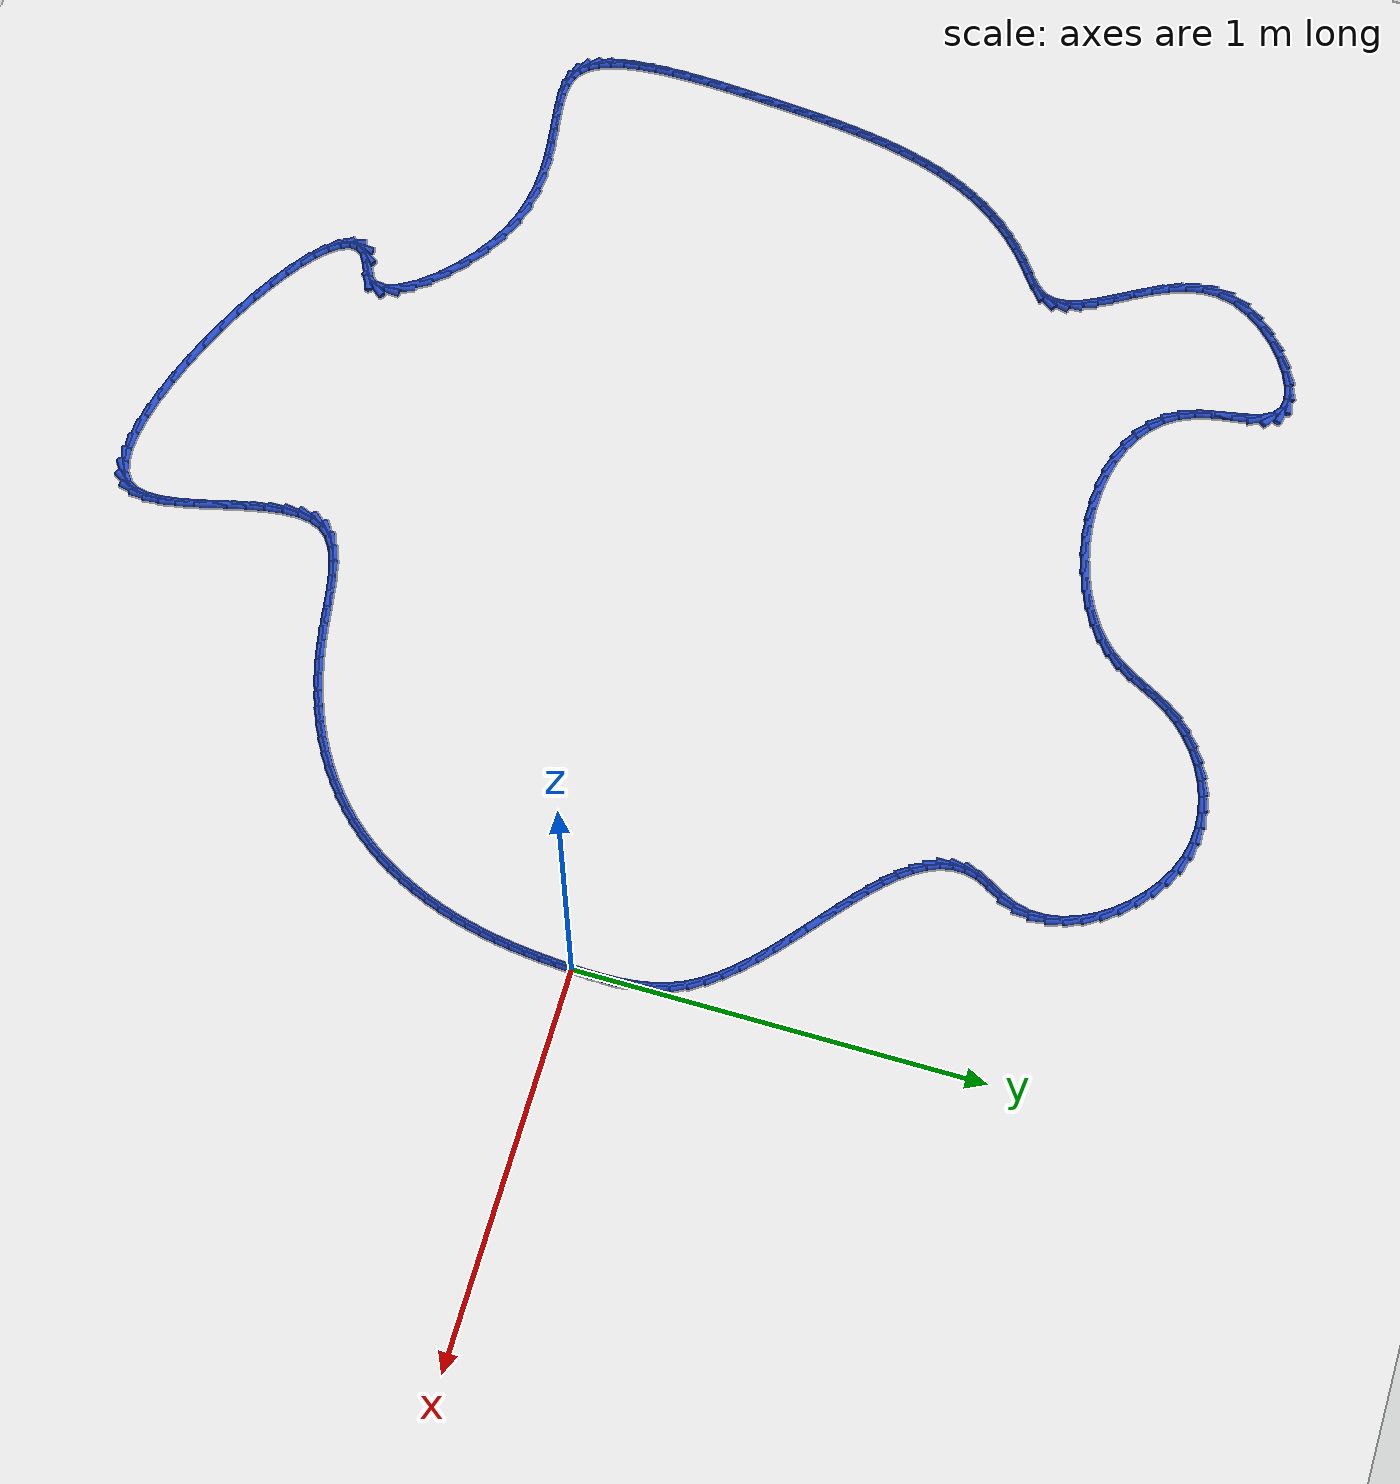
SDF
<sdf version="1.6">
 <world name="default">
  <light name="sun" type="directional">
   <pose>0 0 10 0 -0 0</pose>
   <diffuse>0.8 0.8 0.8 1</diffuse>
   <specular>0.2 0.2 0.2 1</specular>
   <attenuation>
    <range>1000</range>
    <constant>0.9</constant>
    <linear>0.01</linear>
    <quadratic>0.001</quadratic>
   </attenuation>
   <direction>-0.5 0.1 -0.9</direction>
  </light>
  <model name="ground_plane">
   <static>1</static>
   <link name="link">
    <collision name="collision">
     <geometry><plane><normal>0 0 1</normal><size>100 100</size></plane></geometry>
     <surface><friction><ode><mu>100</mu><mu2>50</mu2></ode></friction></surface>
    </collision>
    <visual name="visual">
     <cast_shadows>0</cast_shadows>
     <geometry><plane><normal>0 0 1</normal><size>100 100</size></plane></geometry>
     <material>
      <script><uri>file://media/materials/scripts/gazebo.material</uri><name>Gazebo/WhiteGlow</name></script>
     </material>
    </visual>
   </link>
  </model>
  <gravity>0 0 -9.8</gravity>
  <magnetic_field>6e-06 2.3e-05 -4.2e-05</magnetic_field>
  <atmosphere type="adiabatic"/>
  <physics name="default_physics" default="0" type="ode">
   <max_step_size>0.001</max_step_size>
   <real_time_factor>1</real_time_factor>
   <real_time_update_rate>1000</real_time_update_rate>
  </physics>
  <scene><ambient>0.4 0.4 0.4 1</ambient><background>0.7 0.7 0.7 1</background><shadows>1</shadows></scene>
  <spherical_coordinates>
   <surface_model>EARTH_WGS84</surface_model>
   <latitude_deg>0</latitude_deg>
   <longitude_deg>0</longitude_deg>
   <elevation>0</elevation>
   <heading_deg>0</heading_deg>
  </spherical_coordinates>
  <model name="line">
   <link name="link_0">
    <pose>5.312590645178972e-18 -6.938893903907228e-18 0.01 0 1.57 1.5284120219829822</pose>
    <collision name="collision">
     <geometry><cylinder><radius>0.01</radius><length>0.08</length></cylinder></geometry>
    </collision>
    <visual name="visual">
     <material>
      <script><name>Gazebo/Blue</name><uri>file://media/materials/scripts/gazebo.material</uri></script>
     </material>
     <geometry><cylinder><radius>0.01</radius><length>0.08</length></cylinder></geometry>
    </visual>
   </link>
   <link name="link_1">
    <pose>0.0016449256357191772 0.03878653967538023 0.01 0 1.57 1.5588082013449085</pose>
    <collision name="collision">
     <geometry><cylinder><radius>0.01</radius><length>0.08</length></cylinder></geometry>
    </collision>
    <visual name="visual">
     <material>
      <script><name>Gazebo/Blue</name><uri>file://media/materials/scripts/gazebo.material</uri></script>
     </material>
     <geometry><cylinder><radius>0.01</radius><length>0.08</length></cylinder></geometry>
    </visual>
   </link>
   <link name="link_2">
    <pose>0.0021105790636816914 0.07762756803634187 0.01 0 1.57 -1.536313613372544</pose>
    <collision name="collision">
     <geometry><cylinder><radius>0.01</radius><length>0.08</length></cylinder></geometry>
    </collision>
    <visual name="visual">
     <material>
      <script><name>Gazebo/Blue</name><uri>file://media/materials/scripts/gazebo.material</uri></script>
     </material>
     <geometry><cylinder><radius>0.01</radius><length>0.08</length></cylinder></geometry>
    </visual>
   </link>
   <link name="link_3">
    <pose>0.000775840544802172 0.11631969280149301 0.01 0 1.57 -1.4731354663270184</pose>
    <collision name="collision">
     <geometry><cylinder><radius>0.01</radius><length>0.08</length></cylinder></geometry>
    </collision>
    <visual name="visual">
     <material>
      <script><name>Gazebo/Blue</name><uri>file://media/materials/scripts/gazebo.material</uri></script>
     </material>
     <geometry><cylinder><radius>0.01</radius><length>0.08</length></cylinder></geometry>
    </visual>
   </link>
   <link name="link_4">
    <pose>-0.002980409660004766 0.15465952168944172 0.01 0 1.57 -1.3927614203770944</pose>
    <collision name="collision">
     <geometry><cylinder><radius>0.01</radius><length>0.08</length></cylinder></geometry>
    </collision>
    <visual name="visual">
     <material>
      <script><name>Gazebo/Blue</name><uri>file://media/materials/scripts/gazebo.material</uri></script>
     </material>
     <geometry><cylinder><radius>0.01</radius><length>0.08</length></cylinder></geometry>
    </visual>
   </link>
   <link name="link_5">
    <pose>-0.009779291289824497 0.1924436624187961 0.01 0 1.57 -1.2953945141184164</pose>
    <collision name="collision">
     <geometry><cylinder><radius>0.01</radius><length>0.08</length></cylinder></geometry>
    </collision>
    <visual name="visual">
     <material>
      <script><name>Gazebo/Blue</name><uri>file://media/materials/scripts/gazebo.material</uri></script>
     </material>
     <geometry><cylinder><radius>0.01</radius><length>0.08</length></cylinder></geometry>
    </visual>
   </link>
   <link name="link_6">
    <pose>-0.02024192408374241 0.22946872270816426 0.01 0 1.57 -1.182605247328614</pose>
    <collision name="collision">
     <geometry><cylinder><radius>0.01</radius><length>0.08</length></cylinder></geometry>
    </collision>
    <visual name="visual">
     <material>
      <script><name>Gazebo/Blue</name><uri>file://media/materials/scripts/gazebo.material</uri></script>
     </material>
     <geometry><cylinder><radius>0.01</radius><length>0.08</length></cylinder></geometry>
    </visual>
   </link>
   <link name="link_7">
    <pose>-0.03498942778084387 0.26553131027615423 0.01 0 1.57 -1.061551290668089</pose>
    <collision name="collision">
     <geometry><cylinder><radius>0.01</radius><length>0.08</length></cylinder></geometry>
    </collision>
    <visual name="visual">
     <material>
      <script><name>Gazebo/Blue</name><uri>file://media/materials/scripts/gazebo.material</uri></script>
     </material>
     <geometry><cylinder><radius>0.01</radius><length>0.08</length></cylinder></geometry>
    </visual>
   </link>
   <link name="link_8">
    <pose>-0.05449430506081396 0.3004632527290053 0.01 0 1.57 -0.9562304875554407</pose>
    <collision name="collision">
     <geometry><cylinder><radius>0.01</radius><length>0.08</length></cylinder></geometry>
    </collision>
    <visual name="visual">
     <material>
      <script><name>Gazebo/Blue</name><uri>file://media/materials/scripts/gazebo.material</uri></script>
     </material>
     <geometry><cylinder><radius>0.01</radius><length>0.08</length></cylinder></geometry>
    </visual>
   </link>
   <link name="link_9">
    <pose>-0.07837352738572875 0.3342991250121306 0.01 0 1.57 -0.8726056410686038</pose>
    <collision name="collision">
     <geometry><cylinder><radius>0.01</radius><length>0.08</length></cylinder></geometry>
    </collision>
    <visual name="visual">
     <material>
      <script><name>Gazebo/Blue</name><uri>file://media/materials/scripts/gazebo.material</uri></script>
     </material>
     <geometry><cylinder><radius>0.01</radius><length>0.08</length></cylinder></geometry>
    </visual>
   </link>
   <link name="link_10">
    <pose>-0.10593854981202931 0.36714590461691826 0.01 0 1.57 -0.8078305541972087</pose>
    <collision name="collision">
     <geometry><cylinder><radius>0.01</radius><length>0.08</length></cylinder></geometry>
    </collision>
    <visual name="visual">
     <material>
      <script><name>Gazebo/Blue</name><uri>file://media/materials/scripts/gazebo.material</uri></script>
     </material>
     <geometry><cylinder><radius>0.01</radius><length>0.08</length></cylinder></geometry>
    </visual>
   </link>
   <link name="link_11">
    <pose>-0.1365004468171024 0.3991106592259611 0.01 0 1.57 -0.7591778529824315</pose>
    <collision name="collision">
     <geometry><cylinder><radius>0.01</radius><length>0.08</length></cylinder></geometry>
    </collision>
    <visual name="visual">
     <material>
      <script><name>Gazebo/Blue</name><uri>file://media/materials/scripts/gazebo.material</uri></script>
     </material>
     <geometry><cylinder><radius>0.01</radius><length>0.08</length></cylinder></geometry>
    </visual>
   </link>
   <link name="link_12">
    <pose>-0.1693702928783347 0.43030045652185134 0.01 0 1.57 -0.7244536635141305</pose>
    <collision name="collision">
     <geometry><cylinder><radius>0.01</radius><length>0.08</length></cylinder></geometry>
    </collision>
    <visual name="visual">
     <material>
      <script><name>Gazebo/Blue</name><uri>file://media/materials/scripts/gazebo.material</uri></script>
     </material>
     <geometry><cylinder><radius>0.01</radius><length>0.08</length></cylinder></geometry>
    </visual>
   </link>
   <link name="link_13">
    <pose>-0.2038591624731127 0.46082236418718153 0.01 0 1.57 -0.7021119610644642</pose>
    <collision name="collision">
     <geometry><cylinder><radius>0.01</radius><length>0.08</length></cylinder></geometry>
    </collision>
    <visual name="visual">
     <material>
      <script><name>Gazebo/Blue</name><uri>file://media/materials/scripts/gazebo.material</uri></script>
     </material>
     <geometry><cylinder><radius>0.01</radius><length>0.08</length></cylinder></geometry>
    </visual>
   </link>
   <link name="link_14">
    <pose>-0.23927813007882323 0.4907834499045443 0.01 0 1.57 -0.6912618850647968</pose>
    <collision name="collision">
     <geometry><cylinder><radius>0.01</radius><length>0.08</length></cylinder></geometry>
    </collision>
    <visual name="visual">
     <material>
      <script><name>Gazebo/Blue</name><uri>file://media/materials/scripts/gazebo.material</uri></script>
     </material>
     <geometry><cylinder><radius>0.01</radius><length>0.08</length></cylinder></geometry>
    </visual>
   </link>
   <link name="link_15">
    <pose>-0.2749382701728529 0.5202907813565317 0.01 0 1.57 -0.6916631385065796</pose>
    <collision name="collision">
     <geometry><cylinder><radius>0.01</radius><length>0.08</length></cylinder></geometry>
    </collision>
    <visual name="visual">
     <material>
      <script><name>Gazebo/Blue</name><uri>file://media/materials/scripts/gazebo.material</uri></script>
     </material>
     <geometry><cylinder><radius>0.01</radius><length>0.08</length></cylinder></geometry>
    </visual>
   </link>
   <link name="link_16">
    <pose>-0.3101506572325884 0.5494514262257368 0.01 0 1.57 -0.7037554468040839</pose>
    <collision name="collision">
     <geometry><cylinder><radius>0.01</radius><length>0.08</length></cylinder></geometry>
    </collision>
    <visual name="visual">
     <material>
      <script><name>Gazebo/Blue</name><uri>file://media/materials/scripts/gazebo.material</uri></script>
     </material>
     <geometry><cylinder><radius>0.01</radius><length>0.08</length></cylinder></geometry>
    </visual>
   </link>
   <link name="link_17">
    <pose>-0.3442263657354163 0.5783724521947516 0.01 0 1.57 -0.7287466868001244</pose>
    <collision name="collision">
     <geometry><cylinder><radius>0.01</radius><length>0.08</length></cylinder></geometry>
    </collision>
    <visual name="visual">
     <material>
      <script><name>Gazebo/Blue</name><uri>file://media/materials/scripts/gazebo.material</uri></script>
     </material>
     <geometry><cylinder><radius>0.01</radius><length>0.08</length></cylinder></geometry>
    </visual>
   </link>
   <link name="link_18">
    <pose>-0.37647647015872343 0.6071609269461689 0.01 0 1.57 -0.7687739267215762</pose>
    <collision name="collision">
     <geometry><cylinder><radius>0.01</radius><length>0.08</length></cylinder></geometry>
    </collision>
    <visual name="visual">
     <material>
      <script><name>Gazebo/Blue</name><uri>file://media/materials/scripts/gazebo.material</uri></script>
     </material>
     <geometry><cylinder><radius>0.01</radius><length>0.08</length></cylinder></geometry>
    </visual>
   </link>
   <link name="link_19">
    <pose>-0.40621204497989616 0.6359239181625808 0.01 0 1.57 -0.827132559578673</pose>
    <collision name="collision">
     <geometry><cylinder><radius>0.01</radius><length>0.08</length></cylinder></geometry>
    </collision>
    <visual name="visual">
     <material>
      <script><name>Gazebo/Blue</name><uri>file://media/materials/scripts/gazebo.material</uri></script>
     </material>
     <geometry><cylinder><radius>0.01</radius><length>0.08</length></cylinder></geometry>
    </visual>
   </link>
   <link name="link_20">
    <pose>-0.43274416467632143 0.6647684935265801 0.01 0 1.57 -0.9085023496919414</pose>
    <collision name="collision">
     <geometry><cylinder><radius>0.01</radius><length>0.08</length></cylinder></geometry>
    </collision>
    <visual name="visual">
     <material>
      <script><name>Gazebo/Blue</name><uri>file://media/materials/scripts/gazebo.material</uri></script>
     </material>
     <geometry><cylinder><radius>0.01</radius><length>0.08</length></cylinder></geometry>
    </visual>
   </link>
   <link name="link_21">
    <pose>-0.4553839037253859 0.6938017207207593 0.01 0 1.57 -1.0188977773859</pose>
    <collision name="collision">
     <geometry><cylinder><radius>0.01</radius><length>0.08</length></cylinder></geometry>
    </collision>
    <visual name="visual">
     <material>
      <script><name>Gazebo/Blue</name><uri>file://media/materials/scripts/gazebo.material</uri></script>
     </material>
     <geometry><cylinder><radius>0.01</radius><length>0.08</length></cylinder></geometry>
    </visual>
   </link>
   <link name="link_22">
    <pose>-0.4734423366044761 0.7231306674277107 0.01 0 1.57 -1.1645973447803368</pose>
    <collision name="collision">
     <geometry><cylinder><radius>0.01</radius><length>0.08</length></cylinder></geometry>
    </collision>
    <visual name="visual">
     <material>
      <script><name>Gazebo/Blue</name><uri>file://media/materials/scripts/gazebo.material</uri></script>
     </material>
     <geometry><cylinder><radius>0.01</radius><length>0.08</length></cylinder></geometry>
    </visual>
   </link>
   <link name="link_23">
    <pose>-0.4862305377909788 0.752862401330027 0.01 0 1.57 -1.3487050452910978</pose>
    <collision name="collision">
     <geometry><cylinder><radius>0.01</radius><length>0.08</length></cylinder></geometry>
    </collision>
    <visual name="visual">
     <material>
      <script><name>Gazebo/Blue</name><uri>file://media/materials/scripts/gazebo.material</uri></script>
     </material>
     <geometry><cylinder><radius>0.01</radius><length>0.08</length></cylinder></geometry>
    </visual>
   </link>
   <link name="link_24">
    <pose>-0.4930595817622805 0.7831039901103003 0.01 0 1.57 -1.564932169669321</pose>
    <collision name="collision">
     <geometry><cylinder><radius>0.01</radius><length>0.08</length></cylinder></geometry>
    </collision>
    <visual name="visual">
     <material>
      <script><name>Gazebo/Blue</name><uri>file://media/materials/scripts/gazebo.material</uri></script>
     </material>
     <geometry><cylinder><radius>0.01</radius><length>0.08</length></cylinder></geometry>
    </visual>
   </link>
   <link name="link_25">
    <pose>-0.4932405429957679 0.8139625014511231 0.01 0 1.57 1.347976003183025</pose>
    <collision name="collision">
     <geometry><cylinder><radius>0.01</radius><length>0.08</length></cylinder></geometry>
    </collision>
    <visual name="visual">
     <material>
      <script><name>Gazebo/Blue</name><uri>file://media/materials/scripts/gazebo.material</uri></script>
     </material>
     <geometry><cylinder><radius>0.01</radius><length>0.08</length></cylinder></geometry>
    </visual>
   </link>
   <link name="link_26">
    <pose>-0.48608449596882786 0.8455450030350884 0.01 0 1.57 1.139984625933581</pose>
    <collision name="collision">
     <geometry><cylinder><radius>0.01</radius><length>0.08</length></cylinder></geometry>
    </collision>
    <visual name="visual">
     <material>
      <script><name>Gazebo/Blue</name><uri>file://media/materials/scripts/gazebo.material</uri></script>
     </material>
     <geometry><cylinder><radius>0.01</radius><length>0.08</length></cylinder></geometry>
    </visual>
   </link>
   <link name="link_27">
    <pose>-0.4711798877305397 0.8779742554726534 0.01 0 1.57 1.0559183384728728</pose>
    <collision name="collision">
     <geometry><cylinder><radius>0.01</radius><length>0.08</length></cylinder></geometry>
    </collision>
    <visual name="visual">
     <material>
      <script><name>Gazebo/Blue</name><uri>file://media/materials/scripts/gazebo.material</uri></script>
     </material>
     <geometry><cylinder><radius>0.01</radius><length>0.08</length></cylinder></geometry>
    </visual>
   </link>
   <link name="link_28">
    <pose>-0.4521542267847806 0.911601537643639 0.01 0 1.57 1.1348610680621782</pose>
    <collision name="collision">
     <geometry><cylinder><radius>0.01</radius><length>0.08</length></cylinder></geometry>
    </collision>
    <visual name="visual">
     <material>
      <script><name>Gazebo/Blue</name><uri>file://media/materials/scripts/gazebo.material</uri></script>
     </material>
     <geometry><cylinder><radius>0.01</radius><length>0.08</length></cylinder></geometry>
    </visual>
   </link>
   <link name="link_29">
    <pose>-0.4356876977392102 0.946950760601224 0.01 0 1.57 1.341253518974366</pose>
    <collision name="collision">
     <geometry><cylinder><radius>0.01</radius><length>0.08</length></cylinder></geometry>
    </collision>
    <visual name="visual">
     <material>
      <script><name>Gazebo/Blue</name><uri>file://media/materials/scripts/gazebo.material</uri></script>
     </material>
     <geometry><cylinder><radius>0.01</radius><length>0.08</length></cylinder></geometry>
    </visual>
   </link>
   <link name="link_30">
    <pose>-0.42696664289917663 0.9842742719191184 0.01 0 1.57 1.5522628280849675</pose>
    <collision name="collision">
     <geometry><cylinder><radius>0.01</radius><length>0.08</length></cylinder></geometry>
    </collision>
    <visual name="visual">
     <material>
      <script><name>Gazebo/Blue</name><uri>file://media/materials/scripts/gazebo.material</uri></script>
     </material>
     <geometry><cylinder><radius>0.01</radius><length>0.08</length></cylinder></geometry>
    </visual>
   </link>
   <link name="link_31">
    <pose>-0.42624961150082696 1.0229582414085496 0.01 0 1.57 -1.4047243893705195</pose>
    <collision name="collision">
     <geometry><cylinder><radius>0.01</radius><length>0.08</length></cylinder></geometry>
    </collision>
    <visual name="visual">
     <material>
      <script><name>Gazebo/Blue</name><uri>file://media/materials/scripts/gazebo.material</uri></script>
     </material>
     <geometry><cylinder><radius>0.01</radius><length>0.08</length></cylinder></geometry>
    </visual>
   </link>
   <link name="link_32">
    <pose>-0.432830374694662 1.062219256004236 0.01 0 1.57 -1.245498500117396</pose>
    <collision name="collision">
     <geometry><cylinder><radius>0.01</radius><length>0.08</length></cylinder></geometry>
    </collision>
    <visual name="visual">
     <material>
      <script><name>Gazebo/Blue</name><uri>file://media/materials/scripts/gazebo.material</uri></script>
     </material>
     <geometry><cylinder><radius>0.01</radius><length>0.08</length></cylinder></geometry>
    </visual>
   </link>
   <link name="link_33">
    <pose>-0.4460027036311829 1.1012739026408969 0.01 0 1.57 -1.106618542120685</pose>
    <collision name="collision">
     <geometry><cylinder><radius>0.01</radius><length>0.08</length></cylinder></geometry>
    </collision>
    <visual name="visual">
     <material>
      <script><name>Gazebo/Blue</name><uri>file://media/materials/scripts/gazebo.material</uri></script>
     </material>
     <geometry><cylinder><radius>0.01</radius><length>0.08</length></cylinder></geometry>
    </visual>
   </link>
   <link name="link_34">
    <pose>-0.46506036946089047 1.1393387682532505 0.01 0 1.57 -0.9819867343227149</pose>
    <collision name="collision">
     <geometry><cylinder><radius>0.01</radius><length>0.08</length></cylinder></geometry>
    </collision>
    <visual name="visual">
     <material>
      <script><name>Gazebo/Blue</name><uri>file://media/materials/scripts/gazebo.material</uri></script>
     </material>
     <geometry><cylinder><radius>0.01</radius><length>0.08</length></cylinder></geometry>
    </visual>
   </link>
   <link name="link_35">
    <pose>-0.48929714333428564 1.1756304397760151 0.01 0 1.57 -0.8657028578745892</pose>
    <collision name="collision">
     <geometry><cylinder><radius>0.01</radius><length>0.08</length></cylinder></geometry>
    </collision>
    <visual name="visual">
     <material>
      <script><name>Gazebo/Blue</name><uri>file://media/materials/scripts/gazebo.material</uri></script>
     </material>
     <geometry><cylinder><radius>0.01</radius><length>0.08</length></cylinder></geometry>
    </visual>
   </link>
   <link name="link_36">
    <pose>-0.5180067964018695 1.2093655041439102 0.01 0 1.57 -0.752306785481803</pose>
    <collision name="collision">
     <geometry><cylinder><radius>0.01</radius><length>0.08</length></cylinder></geometry>
    </collision>
    <visual name="visual">
     <material>
      <script><name>Gazebo/Blue</name><uri>file://media/materials/scripts/gazebo.material</uri></script>
     </material>
     <geometry><cylinder><radius>0.01</radius><length>0.08</length></cylinder></geometry>
    </visual>
   </link>
   <link name="link_37">
    <pose>-0.550483099814143 1.2397605482916536 0.01 0 1.57 -0.6366053123781082</pose>
    <collision name="collision">
     <geometry><cylinder><radius>0.01</radius><length>0.08</length></cylinder></geometry>
    </collision>
    <visual name="visual">
     <material>
      <script><name>Gazebo/Blue</name><uri>file://media/materials/scripts/gazebo.material</uri></script>
     </material>
     <geometry><cylinder><radius>0.01</radius><length>0.08</length></cylinder></geometry>
    </visual>
   </link>
   <link name="link_38">
    <pose>-0.5860198247216069 1.2660321591539643 0.01 0 1.57 -0.5134138002548242</pose>
    <collision name="collision">
     <geometry><cylinder><radius>0.01</radius><length>0.08</length></cylinder></geometry>
    </collision>
    <visual name="visual">
     <material>
      <script><name>Gazebo/Blue</name><uri>file://media/materials/scripts/gazebo.material</uri></script>
     </material>
     <geometry><cylinder><radius>0.01</radius><length>0.08</length></cylinder></geometry>
    </visual>
   </link>
   <link name="link_39">
    <pose>-0.6239107422747626 1.287396923665561 0.01 0 1.57 -0.3774273320935404</pose>
    <collision name="collision">
     <geometry><cylinder><radius>0.01</radius><length>0.08</length></cylinder></geometry>
    </collision>
    <visual name="visual">
     <material>
      <script><name>Gazebo/Blue</name><uri>file://media/materials/scripts/gazebo.material</uri></script>
     </material>
     <geometry><cylinder><radius>0.01</radius><length>0.08</length></cylinder></geometry>
    </visual>
   </link>
   <link name="link_40">
    <pose>-0.663449623624111 1.3030714287611622 0.01 0 1.57 -0.22660096215738756</pose>
    <collision name="collision">
     <geometry><cylinder><radius>0.01</radius><length>0.08</length></cylinder></geometry>
    </collision>
    <visual name="visual">
     <material>
      <script><name>Gazebo/Blue</name><uri>file://media/materials/scripts/gazebo.material</uri></script>
     </material>
     <geometry><cylinder><radius>0.01</radius><length>0.08</length></cylinder></geometry>
    </visual>
   </link>
   <link name="link_41">
    <pose>-0.7039492587727624 1.3124090576921918 0.01 0 1.57 -0.07704988709630899</pose>
    <collision name="collision">
     <geometry><cylinder><radius>0.01</radius><length>0.08</length></cylinder></geometry>
    </collision>
    <visual name="visual">
     <material>
      <script><name>Gazebo/Blue</name><uri>file://media/materials/scripts/gazebo.material</uri></script>
     </material>
     <geometry><cylinder><radius>0.01</radius><length>0.08</length></cylinder></geometry>
    </visual>
   </link>
   <link name="link_42">
    <pose>-0.7448339784703472 1.3155654694098442 0.01 0 1.57 0.063193166868156</pose>
    <collision name="collision">
     <geometry><cylinder><radius>0.01</radius><length>0.08</length></cylinder></geometry>
    </collision>
    <visual name="visual">
     <material>
      <script><name>Gazebo/Blue</name><uri>file://media/materials/scripts/gazebo.material</uri></script>
     </material>
     <geometry><cylinder><radius>0.01</radius><length>0.08</length></cylinder></geometry>
    </visual>
   </link>
   <link name="link_43">
    <pose>-0.7855686494167231 1.3129878845488225 0.01 0 1.57 0.19388873700589332</pose>
    <collision name="collision">
     <geometry><cylinder><radius>0.01</radius><length>0.08</length></cylinder></geometry>
    </collision>
    <visual name="visual">
     <material>
      <script><name>Gazebo/Blue</name><uri>file://media/materials/scripts/gazebo.material</uri></script>
     </material>
     <geometry><cylinder><radius>0.01</radius><length>0.08</length></cylinder></geometry>
    </visual>
   </link>
   <link name="link_44">
    <pose>-0.8256181959069561 1.3051239380071156 0.01 0 1.57 0.31616718971435864</pose>
    <collision name="collision">
     <geometry><cylinder><radius>0.01</radius><length>0.08</length></cylinder></geometry>
    </collision>
    <visual name="visual">
     <material>
      <script><name>Gazebo/Blue</name><uri>file://media/materials/scripts/gazebo.material</uri></script>
     </material>
     <geometry><cylinder><radius>0.01</radius><length>0.08</length></cylinder></geometry>
    </visual>
   </link>
   <link name="link_45">
    <pose>-0.8644475422361128 1.2924212646827133 0.01 0 1.57 0.43202203526242683</pose>
    <collision name="collision">
     <geometry><cylinder><radius>0.01</radius><length>0.08</length></cylinder></geometry>
    </collision>
    <visual name="visual">
     <material>
      <script><name>Gazebo/Blue</name><uri>file://media/materials/scripts/gazebo.material</uri></script>
     </material>
     <geometry><cylinder><radius>0.01</radius><length>0.08</length></cylinder></geometry>
    </visual>
   </link>
   <link name="link_46">
    <pose>-0.9015216126992591 1.2753274994736041 0.01 0 1.57 0.5439420498613435</pose>
    <collision name="collision">
     <geometry><cylinder><radius>0.01</radius><length>0.08</length></cylinder></geometry>
    </collision>
    <visual name="visual">
     <material>
      <script><name>Gazebo/Blue</name><uri>file://media/materials/scripts/gazebo.material</uri></script>
     </material>
     <geometry><cylinder><radius>0.01</radius><length>0.08</length></cylinder></geometry>
    </visual>
   </link>
   <link name="link_47">
    <pose>-0.9363053315914616 1.2542902772777773 0.01 0 1.57 0.6547068976025224</pose>
    <collision name="collision">
     <geometry><cylinder><radius>0.01</radius><length>0.08</length></cylinder></geometry>
    </collision>
    <visual name="visual">
     <material>
      <script><name>Gazebo/Blue</name><uri>file://media/materials/scripts/gazebo.material</uri></script>
     </material>
     <geometry><cylinder><radius>0.01</radius><length>0.08</length></cylinder></geometry>
    </visual>
   </link>
   <link name="link_48">
    <pose>-0.9682636232077863 1.2297572329932227 0.01 0 1.57 0.7673051772545425</pose>
    <collision name="collision">
     <geometry><cylinder><radius>0.01</radius><length>0.08</length></cylinder></geometry>
    </collision>
    <visual name="visual">
     <material>
      <script><name>Gazebo/Blue</name><uri>file://media/materials/scripts/gazebo.material</uri></script>
     </material>
     <geometry><cylinder><radius>0.01</radius><length>0.08</length></cylinder></geometry>
    </visual>
   </link>
   <link name="link_49">
    <pose>-0.9968614118432991 1.2021760015179295 0.01 0 1.57 0.8849014976598666</pose>
    <collision name="collision">
     <geometry><cylinder><radius>0.01</radius><length>0.08</length></cylinder></geometry>
    </collision>
    <visual name="visual">
     <material>
      <script><name>Gazebo/Blue</name><uri>file://media/materials/scripts/gazebo.material</uri></script>
     </material>
     <geometry><cylinder><radius>0.01</radius><length>0.08</length></cylinder></geometry>
    </visual>
   </link>
   <link name="link_50">
    <pose>-1.0215638838793204 1.1719942734082684 0.01 0 1.57 0.9976688930900294</pose>
    <collision name="collision">
     <geometry><cylinder><radius>0.01</radius><length>0.08</length></cylinder></geometry>
    </collision>
    <visual name="visual">
     <material>
      <script><name>Gazebo/Blue</name><uri>file://media/materials/scripts/gazebo.material</uri></script>
     </material>
     <geometry><cylinder><radius>0.01</radius><length>0.08</length></cylinder></geometry>
    </visual>
   </link>
   <link name="link_51">
    <pose>-1.0423604154183082 1.139771059640576 0.01 0 1.57 1.0644278926797055</pose>
    <collision name="collision">
     <geometry><cylinder><radius>0.01</radius><length>0.08</length></cylinder></geometry>
    </collision>
    <visual name="visual">
     <material>
      <script><name>Gazebo/Blue</name><uri>file://media/materials/scripts/gazebo.material</uri></script>
     </material>
     <geometry><cylinder><radius>0.01</radius><length>0.08</length></cylinder></geometry>
    </visual>
   </link>
   <link name="link_52">
    <pose>-1.0608625516020889 1.106409865811045 0.01 0 1.57 1.0750551862706945</pose>
    <collision name="collision">
     <geometry><cylinder><radius>0.01</radius><length>0.08</length></cylinder></geometry>
    </collision>
    <visual name="visual">
     <material>
      <script><name>Gazebo/Blue</name><uri>file://media/materials/scripts/gazebo.material</uri></script>
     </material>
     <geometry><cylinder><radius>0.01</radius><length>0.08</length></cylinder></geometry>
    </visual>
   </link>
   <link name="link_53">
    <pose>-1.0789946709633822 1.072880632898038 0.01 0 1.57 1.0292523694744466</pose>
    <collision name="collision">
     <geometry><cylinder><radius>0.01</radius><length>0.08</length></cylinder></geometry>
    </collision>
    <visual name="visual">
     <material>
      <script><name>Gazebo/Blue</name><uri>file://media/materials/scripts/gazebo.material</uri></script>
     </material>
     <geometry><cylinder><radius>0.01</radius><length>0.08</length></cylinder></geometry>
    </visual>
   </link>
   <link name="link_54">
    <pose>-1.0986811520349062 1.0401533018799172 0.01 0 1.57 0.9283586446200401</pose>
    <collision name="collision">
     <geometry><cylinder><radius>0.01</radius><length>0.08</length></cylinder></geometry>
    </collision>
    <visual name="visual">
     <material>
      <script><name>Gazebo/Blue</name><uri>file://media/materials/scripts/gazebo.material</uri></script>
     </material>
     <geometry><cylinder><radius>0.01</radius><length>0.08</length></cylinder></geometry>
    </visual>
   </link>
   <link name="link_55">
    <pose>-1.121846373349381 1.0091978137350452 0.01 0 1.57 0.7889200525842539</pose>
    <collision name="collision">
     <geometry><cylinder><radius>0.01</radius><length>0.08</length></cylinder></geometry>
    </collision>
    <visual name="visual">
     <material>
      <script><name>Gazebo/Blue</name><uri>file://media/materials/scripts/gazebo.material</uri></script>
     </material>
     <geometry><cylinder><radius>0.01</radius><length>0.08</length></cylinder></geometry>
    </visual>
   </link>
   <link name="link_56">
    <pose>-1.1499961409888821 0.9808490637545612 0.01 0 1.57 0.6586563215360689</pose>
    <collision name="collision">
     <geometry><cylinder><radius>0.01</radius><length>0.08</length></cylinder></geometry>
    </collision>
    <visual name="visual">
     <material>
      <script><name>Gazebo/Blue</name><uri>file://media/materials/scripts/gazebo.material</uri></script>
     </material>
     <geometry><cylinder><radius>0.01</radius><length>0.08</length></cylinder></geometry>
    </visual>
   </link>
   <link name="link_57">
    <pose>-1.1829011087535364 0.9553821281779883 0.01 0 1.57 0.5456979792749265</pose>
    <collision name="collision">
     <geometry><cylinder><radius>0.01</radius><length>0.08</length></cylinder></geometry>
    </collision>
    <visual name="visual">
     <material>
      <script><name>Gazebo/Blue</name><uri>file://media/materials/scripts/gazebo.material</uri></script>
     </material>
     <geometry><cylinder><radius>0.01</radius><length>0.08</length></cylinder></geometry>
    </visual>
   </link>
   <link name="link_58">
    <pose>-1.2198823777023107 0.9329270422638208 0.01 0 1.57 0.44613907043595596</pose>
    <collision name="collision">
     <geometry><cylinder><radius>0.01</radius><length>0.08</length></cylinder></geometry>
    </collision>
    <visual name="visual">
     <material>
      <script><name>Gazebo/Blue</name><uri>file://media/materials/scripts/gazebo.material</uri></script>
     </material>
     <geometry><cylinder><radius>0.01</radius><length>0.08</length></cylinder></geometry>
    </visual>
   </link>
   <link name="link_59">
    <pose>-1.2602610481628223 0.9136138410345943 0.01 0 1.57 0.35632409400290016</pose>
    <collision name="collision">
     <geometry><cylinder><radius>0.01</radius><length>0.08</length></cylinder></geometry>
    </collision>
    <visual name="visual">
     <material>
      <script><name>Gazebo/Blue</name><uri>file://media/materials/scripts/gazebo.material</uri></script>
     </material>
     <geometry><cylinder><radius>0.01</radius><length>0.08</length></cylinder></geometry>
    </visual>
   </link>
   <link name="link_60">
    <pose>-1.3033582204626872 0.8975725595128453 0.01 0 1.57 0.27302986229351545</pose>
    <collision name="collision">
     <geometry><cylinder><radius>0.01</radius><length>0.08</length></cylinder></geometry>
    </collision>
    <visual name="visual">
     <material>
      <script><name>Gazebo/Blue</name><uri>file://media/materials/scripts/gazebo.material</uri></script>
     </material>
     <geometry><cylinder><radius>0.01</radius><length>0.08</length></cylinder></geometry>
    </visual>
   </link>
   <link name="link_61">
    <pose>-1.3484949949295237 0.8849332327211092 0.01 0 1.57 0.19341870682490253</pose>
    <collision name="collision">
     <geometry><cylinder><radius>0.01</radius><length>0.08</length></cylinder></geometry>
    </collision>
    <visual name="visual">
     <material>
      <script><name>Gazebo/Blue</name><uri>file://media/materials/scripts/gazebo.material</uri></script>
     </material>
     <geometry><cylinder><radius>0.01</radius><length>0.08</length></cylinder></geometry>
    </visual>
   </link>
   <link name="link_62">
    <pose>-1.394992471890947 0.8758258956819222 0.01 0 1.57 0.11490901057066237</pose>
    <collision name="collision">
     <geometry><cylinder><radius>0.01</radius><length>0.08</length></cylinder></geometry>
    </collision>
    <visual name="visual">
     <material>
      <script><name>Gazebo/Blue</name><uri>file://media/materials/scripts/gazebo.material</uri></script>
     </material>
     <geometry><cylinder><radius>0.01</radius><length>0.08</length></cylinder></geometry>
    </visual>
   </link>
   <link name="link_63">
    <pose>-1.442171751674576 0.87038058341782 0.01 0 1.57 0.03502543224834319</pose>
    <collision name="collision">
     <geometry><cylinder><radius>0.01</radius><length>0.08</length></cylinder></geometry>
    </collision>
    <visual name="visual">
     <material>
      <script><name>Gazebo/Blue</name><uri>file://media/materials/scripts/gazebo.material</uri></script>
     </material>
     <geometry><cylinder><radius>0.01</radius><length>0.08</length></cylinder></geometry>
    </visual>
   </link>
   <link name="link_64">
    <pose>-1.4893539346080258 0.8687273309513387 0.01 0 1.57 -0.04874716901255581</pose>
    <collision name="collision">
     <geometry><cylinder><radius>0.01</radius><length>0.08</length></cylinder></geometry>
    </collision>
    <visual name="visual">
     <material>
      <script><name>Gazebo/Blue</name><uri>file://media/materials/scripts/gazebo.material</uri></script>
     </material>
     <geometry><cylinder><radius>0.01</radius><length>0.08</length></cylinder></geometry>
    </visual>
   </link>
   <link name="link_65">
    <pose>-1.5358601210189131 0.8709961733050139 0.01 0 1.57 -0.13909141387673266</pose>
    <collision name="collision">
     <geometry><cylinder><radius>0.01</radius><length>0.08</length></cylinder></geometry>
    </collision>
    <visual name="visual">
     <material>
      <script><name>Gazebo/Blue</name><uri>file://media/materials/scripts/gazebo.material</uri></script>
     </material>
     <geometry><cylinder><radius>0.01</radius><length>0.08</length></cylinder></geometry>
    </visual>
   </link>
   <link name="link_66">
    <pose>-1.581011411234857 0.877317145501382 0.01 0 1.57 -0.23893989248989606</pose>
    <collision name="collision">
     <geometry><cylinder><radius>0.01</radius><length>0.08</length></cylinder></geometry>
    </collision>
    <visual name="visual">
     <material>
      <script><name>Gazebo/Blue</name><uri>file://media/materials/scripts/gazebo.material</uri></script>
     </material>
     <geometry><cylinder><radius>0.01</radius><length>0.08</length></cylinder></geometry>
    </visual>
   </link>
   <link name="link_67">
    <pose>-1.6241289055834724 0.8878202825629785 0.01 0 1.57 -0.3514501183548127</pose>
    <collision name="collision">
     <geometry><cylinder><radius>0.01</radius><length>0.08</length></cylinder></geometry>
    </collision>
    <visual name="visual">
     <material>
      <script><name>Gazebo/Blue</name><uri>file://media/materials/scripts/gazebo.material</uri></script>
     </material>
     <geometry><cylinder><radius>0.01</radius><length>0.08</length></cylinder></geometry>
    </visual>
   </link>
   <link name="link_68">
    <pose>-1.6645337043923774 0.9026356195123397 0.01 0 1.57 -0.47974694753183705</pose>
    <collision name="collision">
     <geometry><cylinder><radius>0.01</radius><length>0.08</length></cylinder></geometry>
    </collision>
    <visual name="visual">
     <material>
      <script><name>Gazebo/Blue</name><uri>file://media/materials/scripts/gazebo.material</uri></script>
     </material>
     <geometry><cylinder><radius>0.01</radius><length>0.08</length></cylinder></geometry>
    </visual>
   </link>
   <link name="link_69">
    <pose>-1.7015469079891876 0.9218931913720011 0.01 0 1.57 -0.6262404363219375</pose>
    <collision name="collision">
     <geometry><cylinder><radius>0.01</radius><length>0.08</length></cylinder></geometry>
    </collision>
    <visual name="visual">
     <material>
      <script><name>Gazebo/Blue</name><uri>file://media/materials/scripts/gazebo.material</uri></script>
     </material>
     <geometry><cylinder><radius>0.01</radius><length>0.08</length></cylinder></geometry>
    </visual>
   </link>
   <link name="link_70">
    <pose>-1.7344896167015211 0.9457230331644988 0.01 0 1.57 -0.7913712935816095</pose>
    <collision name="collision">
     <geometry><cylinder><radius>0.01</radius><length>0.08</length></cylinder></geometry>
    </collision>
    <visual name="visual">
     <material>
      <script><name>Gazebo/Blue</name><uri>file://media/materials/scripts/gazebo.material</uri></script>
     </material>
     <geometry><cylinder><radius>0.01</radius><length>0.08</length></cylinder></geometry>
    </visual>
   </link>
   <link name="link_71">
    <pose>-1.762682930856994 0.9742551799123687 0.01 0 1.57 -0.9720397861753626</pose>
    <collision name="collision">
     <geometry><cylinder><radius>0.01</radius><length>0.08</length></cylinder></geometry>
    </collision>
    <visual name="visual">
     <material>
      <script><name>Gazebo/Blue</name><uri>file://media/materials/scripts/gazebo.material</uri></script>
     </material>
     <geometry><cylinder><radius>0.01</radius><length>0.08</length></cylinder></geometry>
    </visual>
   </link>
   <link name="link_72">
    <pose>-1.7854479507832237 1.0076196666381472 0.01 0 1.57 -1.160239931327634</pose>
    <collision name="collision">
     <geometry><cylinder><radius>0.01</radius><length>0.08</length></cylinder></geometry>
    </collision>
    <visual name="visual">
     <material>
      <script><name>Gazebo/Blue</name><uri>file://media/materials/scripts/gazebo.material</uri></script>
     </material>
     <geometry><cylinder><radius>0.01</radius><length>0.08</length></cylinder></geometry>
    </visual>
   </link>
   <link name="link_73">
    <pose>-1.8021237760128328 1.0459291050560426 0.01 0 1.57 -1.313152241642247</pose>
    <collision name="collision">
     <geometry><cylinder><radius>0.01</radius><length>0.08</length></cylinder></geometry>
    </collision>
    <visual name="visual">
     <material>
      <script><name>Gazebo/Blue</name><uri>file://media/materials/scripts/gazebo.material</uri></script>
     </material>
     <geometry><cylinder><radius>0.01</radius><length>0.08</length></cylinder></geometry>
    </visual>
   </link>
   <link name="link_74">
    <pose>-1.8132458506718558 1.0881380401374294 0.01 0 1.57 -1.3870518415586446</pose>
    <collision name="collision">
     <geometry><cylinder><radius>0.01</radius><length>0.08</length></cylinder></geometry>
    </collision>
    <visual name="visual">
     <material>
      <script><name>Gazebo/Blue</name><uri>file://media/materials/scripts/gazebo.material</uri></script>
     </material>
     <geometry><cylinder><radius>0.01</radius><length>0.08</length></cylinder></geometry>
    </visual>
   </link>
   <link name="link_75">
    <pose>-1.82127416810431 1.1313380448834156 0.01 0 1.57 -1.388747293466564</pose>
    <collision name="collision">
     <geometry><cylinder><radius>0.01</radius><length>0.08</length></cylinder></geometry>
    </collision>
    <visual name="visual">
     <material>
      <script><name>Gazebo/Blue</name><uri>file://media/materials/scripts/gazebo.material</uri></script>
     </material>
     <geometry><cylinder><radius>0.01</radius><length>0.08</length></cylinder></geometry>
    </visual>
   </link>
   <link name="link_76">
    <pose>-1.8288427617894452 1.1724522206911596 0.01 0 1.57 -1.306151094775137</pose>
    <collision name="collision">
     <geometry><cylinder><radius>0.01</radius><length>0.08</length></cylinder></geometry>
    </collision>
    <visual name="visual">
     <material>
      <script><name>Gazebo/Blue</name><uri>file://media/materials/scripts/gazebo.material</uri></script>
     </material>
     <geometry><cylinder><radius>0.01</radius><length>0.08</length></cylinder></geometry>
    </visual>
   </link>
   <link name="link_77">
    <pose>-1.8385856652065102 1.2084036689578193 0.01 0 1.57 -1.0872774744307023</pose>
    <collision name="collision">
     <geometry><cylinder><radius>0.01</radius><length>0.08</length></cylinder></geometry>
    </collision>
    <visual name="visual">
     <material>
      <script><name>Gazebo/Blue</name><uri>file://media/materials/scripts/gazebo.material</uri></script>
     </material>
     <geometry><cylinder><radius>0.01</radius><length>0.08</length></cylinder></geometry>
    </visual>
   </link>
   <link name="link_78">
    <pose>-1.8531369118347554 1.2361154910805519 0.01 0 1.57 -0.6454386616561509</pose>
    <collision name="collision">
     <geometry><cylinder><radius>0.01</radius><length>0.08</length></cylinder></geometry>
    </collision>
    <visual name="visual">
     <material>
      <script><name>Gazebo/Blue</name><uri>file://media/materials/scripts/gazebo.material</uri></script>
     </material>
     <geometry><cylinder><radius>0.01</radius><length>0.08</length></cylinder></geometry>
    </visual>
   </link>
   <link name="link_79">
    <pose>-1.8750308689683424 1.2526023378159492 0.01 0 1.57 -0.1489024832219367</pose>
    <collision name="collision">
     <geometry><cylinder><radius>0.01</radius><length>0.08</length></cylinder></geometry>
    </collision>
    <visual name="visual">
     <material>
      <script><name>Gazebo/Blue</name><uri>file://media/materials/scripts/gazebo.material</uri></script>
     </material>
     <geometry><cylinder><radius>0.01</radius><length>0.08</length></cylinder></geometry>
    </visual>
   </link>
   <link name="link_80">
    <pose>-1.9044721229121937 1.257018903276329 0.01 0 1.57 0.17998443423507343</pose>
    <collision name="collision">
     <geometry><cylinder><radius>0.01</radius><length>0.08</length></cylinder></geometry>
    </collision>
    <visual name="visual">
     <material>
      <script><name>Gazebo/Blue</name><uri>file://media/materials/scripts/gazebo.material</uri></script>
     </material>
     <geometry><cylinder><radius>0.01</radius><length>0.08</length></cylinder></geometry>
    </visual>
   </link>
   <link name="link_81">
    <pose>-1.9393144765798844 1.2506792168937835 0.01 0 1.57 0.3915555624367051</pose>
    <collision name="collision">
     <geometry><cylinder><radius>0.01</radius><length>0.08</length></cylinder></geometry>
    </collision>
    <visual name="visual">
     <material>
      <script><name>Gazebo/Blue</name><uri>file://media/materials/scripts/gazebo.material</uri></script>
     </material>
     <geometry><cylinder><radius>0.01</radius><length>0.08</length></cylinder></geometry>
    </visual>
   </link>
   <link name="link_82">
    <pose>-1.977307866113426 1.2349927159500629 0.01 0 1.57 0.5458324565909884</pose>
    <collision name="collision">
     <geometry><cylinder><radius>0.01</radius><length>0.08</length></cylinder></geometry>
    </collision>
    <visual name="visual">
     <material>
      <script><name>Gazebo/Blue</name><uri>file://media/materials/scripts/gazebo.material</uri></script>
     </material>
     <geometry><cylinder><radius>0.01</radius><length>0.08</length></cylinder></geometry>
    </visual>
   </link>
   <link name="link_83">
    <pose>-2.0162022276548353 1.2113688377269194 0.01 0 1.57 0.6766155728892855</pose>
    <collision name="collision">
     <geometry><cylinder><radius>0.01</radius><length>0.08</length></cylinder></geometry>
    </collision>
    <visual name="visual">
     <material>
      <script><name>Gazebo/Blue</name><uri>file://media/materials/scripts/gazebo.material</uri></script>
     </material>
     <geometry><cylinder><radius>0.01</radius><length>0.08</length></cylinder></geometry>
    </visual>
   </link>
   <link name="link_84">
    <pose>-2.0537474973461216 1.181217019506104 0.01 0 1.57 0.804527224765265</pose>
    <collision name="collision">
     <geometry><cylinder><radius>0.01</radius><length>0.08</length></cylinder></geometry>
    </collision>
    <visual name="visual">
     <material>
      <script><name>Gazebo/Blue</name><uri>file://media/materials/scripts/gazebo.material</uri></script>
     </material>
     <geometry><cylinder><radius>0.01</radius><length>0.08</length></cylinder></geometry>
    </visual>
   </link>
   <link name="link_85">
    <pose>-2.0876936113293008 1.1459466985693674 0.01 0 1.57 0.9462372717508026</pose>
    <collision name="collision">
     <geometry><cylinder><radius>0.01</radius><length>0.08</length></cylinder></geometry>
    </collision>
    <visual name="visual">
     <material>
      <script><name>Gazebo/Blue</name><uri>file://media/materials/scripts/gazebo.material</uri></script>
     </material>
     <geometry><cylinder><radius>0.01</radius><length>0.08</length></cylinder></geometry>
    </visual>
   </link>
   <link name="link_86">
    <pose>-2.1157905057463857 1.1069673121984616 0.01 0 1.57 1.119666074090778</pose>
    <collision name="collision">
     <geometry><cylinder><radius>0.01</radius><length>0.08</length></cylinder></geometry>
    </collision>
    <visual name="visual">
     <material>
      <script><name>Gazebo/Blue</name><uri>file://media/materials/scripts/gazebo.material</uri></script>
     </material>
     <geometry><cylinder><radius>0.01</radius><length>0.08</length></cylinder></geometry>
    </visual>
   </link>
   <link name="link_87">
    <pose>-2.135788116739389 1.0656882976751374 0.01 0 1.57 1.3438183965602193</pose>
    <collision name="collision">
     <geometry><cylinder><radius>0.01</radius><length>0.08</length></cylinder></geometry>
    </collision>
    <visual name="visual">
     <material>
      <script><name>Gazebo/Blue</name><uri>file://media/materials/scripts/gazebo.material</uri></script>
     </material>
     <geometry><cylinder><radius>0.01</radius><length>0.08</length></cylinder></geometry>
    </visual>
   </link>
   <link name="link_88">
    <pose>-2.1455334714453587 1.0234929170790426 0.01 0 1.57 -1.5573171466898221</pose>
    <collision name="collision">
     <geometry><cylinder><radius>0.01</radius><length>0.08</length></cylinder></geometry>
    </collision>
    <visual name="visual">
     <material>
      <script><name>Gazebo/Blue</name><uri>file://media/materials/scripts/gazebo.material</uri></script>
     </material>
     <geometry><cylinder><radius>0.01</radius><length>0.08</length></cylinder></geometry>
    </visual>
   </link>
   <link name="link_89">
    <pose>-2.144963377079426 0.9812010391918702 0.01 0 1.57 -1.361707097125111</pose>
    <collision name="collision">
     <geometry><cylinder><radius>0.01</radius><length>0.08</length></cylinder></geometry>
    </collision>
    <visual name="visual">
     <material>
      <script><name>Gazebo/Blue</name><uri>file://media/materials/scripts/gazebo.material</uri></script>
     </material>
     <geometry><cylinder><radius>0.01</radius><length>0.08</length></cylinder></geometry>
    </visual>
   </link>
   <link name="link_90">
    <pose>-2.1360277735934106 0.939089803202066 0.01 0 1.57 -1.2195968500944359</pose>
    <collision name="collision">
     <geometry><cylinder><radius>0.01</radius><length>0.08</length></cylinder></geometry>
    </collision>
    <visual name="visual">
     <material>
      <script><name>Gazebo/Blue</name><uri>file://media/materials/scripts/gazebo.material</uri></script>
     </material>
     <geometry><cylinder><radius>0.01</radius><length>0.08</length></cylinder></geometry>
    </visual>
   </link>
   <link name="link_91">
    <pose>-2.1207583557557816 0.8974143076459268 0.01 0 1.57 -1.1252830928558124</pose>
    <collision name="collision">
     <geometry><cylinder><radius>0.01</radius><length>0.08</length></cylinder></geometry>
    </collision>
    <visual name="visual">
     <material>
      <script><name>Gazebo/Blue</name><uri>file://media/materials/scripts/gazebo.material</uri></script>
     </material>
     <geometry><cylinder><radius>0.01</radius><length>0.08</length></cylinder></geometry>
    </visual>
   </link>
   <link name="link_92">
    <pose>-2.101186818335008 0.8564296510597468 0.01 0 1.57 -1.0713983868236119</pose>
    <collision name="collision">
     <geometry><cylinder><radius>0.01</radius><length>0.08</length></cylinder></geometry>
    </collision>
    <visual name="visual">
     <material>
      <script><name>Gazebo/Blue</name><uri>file://media/materials/scripts/gazebo.material</uri></script>
     </material>
     <geometry><cylinder><radius>0.01</radius><length>0.08</length></cylinder></geometry>
    </visual>
   </link>
   <link name="link_93">
    <pose>-2.0793448560995587 0.8163909319798225 0.01 0 1.57 -1.0538320956029923</pose>
    <collision name="collision">
     <geometry><cylinder><radius>0.01</radius><length>0.08</length></cylinder></geometry>
    </collision>
    <visual name="visual">
     <material>
      <script><name>Gazebo/Blue</name><uri>file://media/materials/scripts/gazebo.material</uri></script>
     </material>
     <geometry><cylinder><radius>0.01</radius><length>0.08</length></cylinder></geometry>
    </visual>
   </link>
   <link name="link_94">
    <pose>-2.057264163817901 0.777553248942448 0.01 0 1.57 -1.0735592627752162</pose>
    <collision name="collision">
     <geometry><cylinder><radius>0.01</radius><length>0.08</length></cylinder></geometry>
    </collision>
    <visual name="visual">
     <material>
      <script><name>Gazebo/Blue</name><uri>file://media/materials/scripts/gazebo.material</uri></script>
     </material>
     <geometry><cylinder><radius>0.01</radius><length>0.08</length></cylinder></geometry>
    </visual>
   </link>
   <link name="link_95">
    <pose>-2.0369764362585046 0.74017170048392 0.01 0 1.57 -1.138392119569944</pose>
    <collision name="collision">
     <geometry><cylinder><radius>0.01</radius><length>0.08</length></cylinder></geometry>
    </collision>
    <visual name="visual">
     <material>
      <script><name>Gazebo/Blue</name><uri>file://media/materials/scripts/gazebo.material</uri></script>
     </material>
     <geometry><cylinder><radius>0.01</radius><length>0.08</length></cylinder></geometry>
    </visual>
   </link>
   <link name="link_96">
    <pose>-2.020513368189838 0.7045013851405328 0.01 0 1.57 -1.26590655161999</pose>
    <collision name="collision">
     <geometry><cylinder><radius>0.01</radius><length>0.08</length></cylinder></geometry>
    </collision>
    <visual name="visual">
     <material>
      <script><name>Gazebo/Blue</name><uri>file://media/materials/scripts/gazebo.material</uri></script>
     </material>
     <geometry><cylinder><radius>0.01</radius><length>0.08</length></cylinder></geometry>
    </visual>
   </link>
   <link name="link_97">
    <pose>-2.0099066543803694 0.6707974014485827 0.01 0 1.57 -1.4846553773351137</pose>
    <collision name="collision">
     <geometry><cylinder><radius>0.01</radius><length>0.08</length></cylinder></geometry>
    </collision>
    <visual name="visual">
     <material>
      <script><name>Gazebo/Blue</name><uri>file://media/materials/scripts/gazebo.material</uri></script>
     </material>
     <geometry><cylinder><radius>0.01</radius><length>0.08</length></cylinder></geometry>
    </visual>
   </link>
   <link name="link_98">
    <pose>-2.0071879895985685 0.6393148479443647 0.01 0 1.57 1.3274545738007524</pose>
    <collision name="collision">
     <geometry><cylinder><radius>0.01</radius><length>0.08</length></cylinder></geometry>
    </collision>
    <visual name="visual">
     <material>
      <script><name>Gazebo/Blue</name><uri>file://media/materials/scripts/gazebo.material</uri></script>
     </material>
     <geometry><cylinder><radius>0.01</radius><length>0.08</length></cylinder></geometry>
    </visual>
   </link>
   <link name="link_99">
    <pose>-2.014389068612903 0.6103088231641736 0.01 0 1.57 0.9417489075000196</pose>
    <collision name="collision">
     <geometry><cylinder><radius>0.01</radius><length>0.08</length></cylinder></geometry>
    </collision>
    <visual name="visual">
     <material>
      <script><name>Gazebo/Blue</name><uri>file://media/materials/scripts/gazebo.material</uri></script>
     </material>
     <geometry><cylinder><radius>0.01</radius><length>0.08</length></cylinder></geometry>
    </visual>
   </link>
   <link name="link_100">
    <pose>-2.0335126682295357 0.5840277513129495 0.01 0 1.57 0.6838257862746775</pose>
    <collision name="collision">
     <geometry><cylinder><radius>0.01</radius><length>0.08</length></cylinder></geometry>
    </collision>
    <visual name="visual">
     <material>
      <script><name>Gazebo/Blue</name><uri>file://media/materials/scripts/gazebo.material</uri></script>
     </material>
     <geometry><cylinder><radius>0.01</radius><length>0.08</length></cylinder></geometry>
    </visual>
   </link>
   <link name="link_101">
    <pose>-2.063093020599734 0.5599195086142398 0.01 0 1.57 0.6436396736419255</pose>
    <collision name="collision">
     <geometry><cylinder><radius>0.01</radius><length>0.08</length></cylinder></geometry>
    </collision>
    <visual name="visual">
     <material>
      <script><name>Gazebo/Blue</name><uri>file://media/materials/scripts/gazebo.material</uri></script>
     </material>
     <geometry><cylinder><radius>0.01</radius><length>0.08</length></cylinder></geometry>
    </visual>
   </link>
   <link name="link_102">
    <pose>-2.0950871230902983 0.5359170040607455 0.01 0 1.57 0.7020694080335425</pose>
    <collision name="collision">
     <geometry><cylinder><radius>0.01</radius><length>0.08</length></cylinder></geometry>
    </collision>
    <visual name="visual">
     <material>
      <script><name>Gazebo/Blue</name><uri>file://media/materials/scripts/gazebo.material</uri></script>
     </material>
     <geometry><cylinder><radius>0.01</radius><length>0.08</length></cylinder></geometry>
    </visual>
   </link>
   <link name="link_103">
    <pose>-2.1247730586447675 0.5108076865131468 0.01 0 1.57 0.767039312121193</pose>
    <collision name="collision">
     <geometry><cylinder><radius>0.01</radius><length>0.08</length></cylinder></geometry>
    </collision>
    <visual name="visual">
     <material>
      <script><name>Gazebo/Blue</name><uri>file://media/materials/scripts/gazebo.material</uri></script>
     </material>
     <geometry><cylinder><radius>0.01</radius><length>0.08</length></cylinder></geometry>
    </visual>
   </link>
   <link name="link_104">
    <pose>-2.152024797814912 0.484538637932432 0.01 0 1.57 0.8328126675281174</pose>
    <collision name="collision">
     <geometry><cylinder><radius>0.01</radius><length>0.08</length></cylinder></geometry>
    </collision>
    <visual name="visual">
     <material>
      <script><name>Gazebo/Blue</name><uri>file://media/materials/scripts/gazebo.material</uri></script>
     </material>
     <geometry><cylinder><radius>0.01</radius><length>0.08</length></cylinder></geometry>
    </visual>
   </link>
   <link name="link_105">
    <pose>-2.1769605747135174 0.45711857279428325 0.01 0 1.57 0.8984476435985272</pose>
    <collision name="collision">
     <geometry><cylinder><radius>0.01</radius><length>0.08</length></cylinder></geometry>
    </collision>
    <visual name="visual">
     <material>
      <script><name>Gazebo/Blue</name><uri>file://media/materials/scripts/gazebo.material</uri></script>
     </material>
     <geometry><cylinder><radius>0.01</radius><length>0.08</length></cylinder></geometry>
    </visual>
   </link>
   <link name="link_106">
    <pose>-2.199698623453371 0.42855620557438423 0.01 0 1.57 0.9629830033524637</pose>
    <collision name="collision">
     <geometry><cylinder><radius>0.01</radius><length>0.08</length></cylinder></geometry>
    </collision>
    <visual name="visual">
     <material>
      <script><name>Gazebo/Blue</name><uri>file://media/materials/scripts/gazebo.material</uri></script>
     </material>
     <geometry><cylinder><radius>0.01</radius><length>0.08</length></cylinder></geometry>
    </visual>
   </link>
   <link name="link_107">
    <pose>-2.2203571781472586 0.39886025074841763 0.01 0 1.57 1.025505269897224</pose>
    <collision name="collision">
     <geometry><cylinder><radius>0.01</radius><length>0.08</length></cylinder></geometry>
    </collision>
    <visual name="visual">
     <material>
      <script><name>Gazebo/Blue</name><uri>file://media/materials/scripts/gazebo.material</uri></script>
     </material>
     <geometry><cylinder><radius>0.01</radius><length>0.08</length></cylinder></geometry>
    </visual>
   </link>
   <link name="link_108">
    <pose>-2.239054472907968 0.36803942279206625 0.01 0 1.57 1.0852076110525115</pose>
    <collision name="collision">
     <geometry><cylinder><radius>0.01</radius><length>0.08</length></cylinder></geometry>
    </collision>
    <visual name="visual">
     <material>
      <script><name>Gazebo/Blue</name><uri>file://media/materials/scripts/gazebo.material</uri></script>
     </material>
     <geometry><cylinder><radius>0.01</radius><length>0.08</length></cylinder></geometry>
    </visual>
   </link>
   <link name="link_109">
    <pose>-2.255908741848285 0.3361024361810137 0.01 0 1.57 1.1414314305284285</pose>
    <collision name="collision">
     <geometry><cylinder><radius>0.01</radius><length>0.08</length></cylinder></geometry>
    </collision>
    <visual name="visual">
     <material>
      <script><name>Gazebo/Blue</name><uri>file://media/materials/scripts/gazebo.material</uri></script>
     </material>
     <geometry><cylinder><radius>0.01</radius><length>0.08</length></cylinder></geometry>
    </visual>
   </link>
   <link name="link_110">
    <pose>-2.2710382190809963 0.3030580053909425 0.01 0 1.57 1.193686564962468</pose>
    <collision name="collision">
     <geometry><cylinder><radius>0.01</radius><length>0.08</length></cylinder></geometry>
    </collision>
    <visual name="visual">
     <material>
      <script><name>Gazebo/Blue</name><uri>file://media/materials/scripts/gazebo.material</uri></script>
     </material>
     <geometry><cylinder><radius>0.01</radius><length>0.08</length></cylinder></geometry>
    </visual>
   </link>
   <link name="link_111">
    <pose>-2.2845611387188884 0.26891484489753636 0.01 0 1.57 1.2416511712960887</pose>
    <collision name="collision">
     <geometry><cylinder><radius>0.01</radius><length>0.08</length></cylinder></geometry>
    </collision>
    <visual name="visual">
     <material>
      <script><name>Gazebo/Blue</name><uri>file://media/materials/scripts/gazebo.material</uri></script>
     </material>
     <geometry><cylinder><radius>0.01</radius><length>0.08</length></cylinder></geometry>
    </visual>
   </link>
   <link name="link_112">
    <pose>-2.296595734874748 0.2336816691764774 0.01 0 1.57 1.285156067237017</pose>
    <collision name="collision">
     <geometry><cylinder><radius>0.01</radius><length>0.08</length></cylinder></geometry>
    </collision>
    <visual name="visual">
     <material>
      <script><name>Gazebo/Blue</name><uri>file://media/materials/scripts/gazebo.material</uri></script>
     </material>
     <geometry><cylinder><radius>0.01</radius><length>0.08</length></cylinder></geometry>
    </visual>
   </link>
   <link name="link_113">
    <pose>-2.3072602416613606 0.19736719270344968 0.01 0 1.57 1.3241597520328656</pose>
    <collision name="collision">
     <geometry><cylinder><radius>0.01</radius><length>0.08</length></cylinder></geometry>
    </collision>
    <visual name="visual">
     <material>
      <script><name>Gazebo/Blue</name><uri>file://media/materials/scripts/gazebo.material</uri></script>
     </material>
     <geometry><cylinder><radius>0.01</radius><length>0.08</length></cylinder></geometry>
    </visual>
   </link>
   <link name="link_114">
    <pose>-2.3166728931915146 0.1599801299541351 0.01 0 1.57 1.358719913734218</pose>
    <collision name="collision">
     <geometry><cylinder><radius>0.01</radius><length>0.08</length></cylinder></geometry>
    </collision>
    <visual name="visual">
     <material>
      <script><name>Gazebo/Blue</name><uri>file://media/materials/scripts/gazebo.material</uri></script>
     </material>
     <geometry><cylinder><radius>0.01</radius><length>0.08</length></cylinder></geometry>
    </visual>
   </link>
   <link name="link_115">
    <pose>-2.3249519235779954 0.12152919540421783 0.01 0 1.57 1.3889657544582772</pose>
    <collision name="collision">
     <geometry><cylinder><radius>0.01</radius><length>0.08</length></cylinder></geometry>
    </collision>
    <visual name="visual">
     <material>
      <script><name>Gazebo/Blue</name><uri>file://media/materials/scripts/gazebo.material</uri></script>
     </material>
     <geometry><cylinder><radius>0.01</radius><length>0.08</length></cylinder></geometry>
    </visual>
   </link>
   <link name="link_116">
    <pose>-2.3322155669335896 0.08202310352938039 0.01 0 1.57 1.4150737402939961</pose>
    <collision name="collision">
     <geometry><cylinder><radius>0.01</radius><length>0.08</length></cylinder></geometry>
    </collision>
    <visual name="visual">
     <material>
      <script><name>Gazebo/Blue</name><uri>file://media/materials/scripts/gazebo.material</uri></script>
     </material>
     <geometry><cylinder><radius>0.01</radius><length>0.08</length></cylinder></geometry>
    </visual>
   </link>
   <link name="link_117">
    <pose>-2.3385820573710836 0.04147056880530478 0.01 0 1.57 1.4372479140591885</pose>
    <collision name="collision">
     <geometry><cylinder><radius>0.01</radius><length>0.08</length></cylinder></geometry>
    </collision>
    <visual name="visual">
     <material>
      <script><name>Gazebo/Blue</name><uri>file://media/materials/scripts/gazebo.material</uri></script>
     </material>
     <geometry><cylinder><radius>0.01</radius><length>0.08</length></cylinder></geometry>
    </visual>
   </link>
   <link name="link_118">
    <pose>-2.3441696290032654 -0.0001196942923239186 0.01 0 1.57 1.4557048907277026</pose>
    <collision name="collision">
     <geometry><cylinder><radius>0.01</radius><length>0.08</length></cylinder></geometry>
    </collision>
    <visual name="visual">
     <material>
      <script><name>Gazebo/Blue</name><uri>file://media/materials/scripts/gazebo.material</uri></script>
     </material>
     <geometry><cylinder><radius>0.01</radius><length>0.08</length></cylinder></geometry>
    </visual>
   </link>
   <link name="link_119">
    <pose>-2.3490965159429185 -0.042738971287823696 0.01 0 1.57 1.4706630727484202</pose>
    <collision name="collision">
     <geometry><cylinder><radius>0.01</radius><length>0.08</length></cylinder></geometry>
    </collision>
    <visual name="visual">
     <material>
      <script><name>Gazebo/Blue</name><uri>file://media/materials/scripts/gazebo.material</uri></script>
     </material>
     <geometry><cylinder><radius>0.01</radius><length>0.08</length></cylinder></geometry>
    </visual>
   </link>
   <link name="link_120">
    <pose>-2.353480952302833 -0.0863785477055115 0.01 0 1.57 1.4823353695530652</pose>
    <collision name="collision">
     <geometry><cylinder><radius>0.01</radius><length>0.08</length></cylinder></geometry>
    </collision>
    <visual name="visual">
     <material>
      <script><name>Gazebo/Blue</name><uri>file://media/materials/scripts/gazebo.material</uri></script>
     </material>
     <geometry><cylinder><radius>0.01</radius><length>0.08</length></cylinder></geometry>
    </visual>
   </link>
   <link name="link_121">
    <pose>-2.3574411721957933 -0.13102970906970432 0.01 0 1.57 1.4909246622306453</pose>
    <collision name="collision">
     <geometry><cylinder><radius>0.01</radius><length>0.08</length></cylinder></geometry>
    </collision>
    <visual name="visual">
     <material>
      <script><name>Gazebo/Blue</name><uri>file://media/materials/scripts/gazebo.material</uri></script>
     </material>
     <geometry><cylinder><radius>0.01</radius><length>0.08</length></cylinder></geometry>
    </visual>
   </link>
   <link name="link_122">
    <pose>-2.3610954097345864 -0.17668374090472028 0.01 0 1.57 1.4966214408377763</pose>
    <collision name="collision">
     <geometry><cylinder><radius>0.01</radius><length>0.08</length></cylinder></geometry>
    </collision>
    <visual name="visual">
     <material>
      <script><name>Gazebo/Blue</name><uri>file://media/materials/scripts/gazebo.material</uri></script>
     </material>
     <geometry><cylinder><radius>0.01</radius><length>0.08</length></cylinder></geometry>
    </visual>
   </link>
   <link name="link_123">
    <pose>-2.364561892870968 -0.2233319201136455 0.01 0 1.57 1.5011227937123892</pose>
    <collision name="collision">
     <geometry><cylinder><radius>0.01</radius><length>0.08</length></cylinder></geometry>
    </collision>
    <visual name="visual">
     <material>
      <script><name>Gazebo/Blue</name><uri>file://media/materials/scripts/gazebo.material</uri></script>
     </material>
     <geometry><cylinder><radius>0.01</radius><length>0.08</length></cylinder></geometry>
    </visual>
   </link>
   <link name="link_124">
    <pose>-2.3678781992594775 -0.27085266834210087 0.01 0 1.57 1.5098568631525529</pose>
    <collision name="collision">
     <geometry><cylinder><radius>0.01</radius><length>0.08</length></cylinder></geometry>
    </collision>
    <visual name="visual">
     <material>
      <script><name>Gazebo/Blue</name><uri>file://media/materials/scripts/gazebo.material</uri></script>
     </material>
     <geometry><cylinder><radius>0.01</radius><length>0.08</length></cylinder></geometry>
    </visual>
   </link>
   <link name="link_125">
    <pose>-2.370799377847863 -0.3187290602742456 0.01 0 1.57 1.5242347103777683</pose>
    <collision name="collision">
     <geometry><cylinder><radius>0.01</radius><length>0.08</length></cylinder></geometry>
    </collision>
    <visual name="visual">
     <material>
      <script><name>Gazebo/Blue</name><uri>file://media/materials/scripts/gazebo.material</uri></script>
     </material>
     <geometry><cylinder><radius>0.01</radius><length>0.08</length></cylinder></geometry>
    </visual>
   </link>
   <link name="link_126">
    <pose>-2.373018645916731 -0.36635764854836866 0.01 0 1.57 1.5449225864542464</pose>
    <collision name="collision">
     <geometry><cylinder><radius>0.01</radius><length>0.08</length></cylinder></geometry>
    </collision>
    <visual name="visual">
     <material>
      <script><name>Gazebo/Blue</name><uri>file://media/materials/scripts/gazebo.material</uri></script>
     </material>
     <geometry><cylinder><radius>0.01</radius><length>0.08</length></cylinder></geometry>
    </visual>
   </link>
   <link name="link_127">
    <pose>-2.3742292207466855 -0.413134985802755 0.01 0 1.57 -1.5684817894324974</pose>
    <collision name="collision">
     <geometry><cylinder><radius>0.01</radius><length>0.08</length></cylinder></geometry>
    </collision>
    <visual name="visual">
     <material>
      <script><name>Gazebo/Blue</name><uri>file://media/materials/scripts/gazebo.material</uri></script>
     </material>
     <geometry><cylinder><radius>0.01</radius><length>0.08</length></cylinder></geometry>
    </visual>
   </link>
   <link name="link_128">
    <pose>-2.37412431961833 -0.4584576246756931 0.01 0 1.57 -1.5308965604337852</pose>
    <collision name="collision">
     <geometry><cylinder><radius>0.01</radius><length>0.08</length></cylinder></geometry>
    </collision>
    <visual name="visual">
     <material>
      <script><name>Gazebo/Blue</name><uri>file://media/materials/scripts/gazebo.material</uri></script>
     </material>
     <geometry><cylinder><radius>0.01</radius><length>0.08</length></cylinder></geometry>
    </visual>
   </link>
   <link name="link_129">
    <pose>-2.37239715981227 -0.5017221178054706 0.01 0 1.57 -1.4809907519672232</pose>
    <collision name="collision">
     <geometry><cylinder><radius>0.01</radius><length>0.08</length></cylinder></geometry>
    </collision>
    <visual name="visual">
     <material>
      <script><name>Gazebo/Blue</name><uri>file://media/materials/scripts/gazebo.material</uri></script>
     </material>
     <geometry><cylinder><radius>0.01</radius><length>0.08</length></cylinder></geometry>
    </visual>
   </link>
   <link name="link_130">
    <pose>-2.3687409586091084 -0.5423250178303746 0.01 0 1.57 -1.4142839808436345</pose>
    <collision name="collision">
     <geometry><cylinder><radius>0.01</radius><length>0.08</length></cylinder></geometry>
    </collision>
    <visual name="visual">
     <material>
      <script><name>Gazebo/Blue</name><uri>file://media/materials/scripts/gazebo.material</uri></script>
     </material>
     <geometry><cylinder><radius>0.01</radius><length>0.08</length></cylinder></geometry>
    </visual>
   </link>
   <link name="link_131">
    <pose>-2.362848933289451 -0.5796628773886937 0.01 0 1.57 -1.3239263520003977</pose>
    <collision name="collision">
     <geometry><cylinder><radius>0.01</radius><length>0.08</length></cylinder></geometry>
    </collision>
    <visual name="visual">
     <material>
      <script><name>Gazebo/Blue</name><uri>file://media/materials/scripts/gazebo.material</uri></script>
     </material>
     <geometry><cylinder><radius>0.01</radius><length>0.08</length></cylinder></geometry>
    </visual>
   </link>
   <link name="link_132">
    <pose>-2.3544143011339003 -0.6131322491187133 0.01 0 1.57 -1.1996881534728057</pose>
    <collision name="collision">
     <geometry><cylinder><radius>0.01</radius><length>0.08</length></cylinder></geometry>
    </collision>
    <visual name="visual">
     <material>
      <script><name>Gazebo/Blue</name><uri>file://media/materials/scripts/gazebo.material</uri></script>
     </material>
     <geometry><cylinder><radius>0.01</radius><length>0.08</length></cylinder></geometry>
    </visual>
   </link>
   <link name="link_133">
    <pose>-2.343130279423063 -0.6421296856587222 0.01 0 1.57 -1.027708167240378</pose>
    <collision name="collision">
     <geometry><cylinder><radius>0.01</radius><length>0.08</length></cylinder></geometry>
    </collision>
    <visual name="visual">
     <material>
      <script><name>Gazebo/Blue</name><uri>file://media/materials/scripts/gazebo.material</uri></script>
     </material>
     <geometry><cylinder><radius>0.01</radius><length>0.08</length></cylinder></geometry>
    </visual>
   </link>
   <link name="link_134">
    <pose>-2.328690085437541 -0.6660517396470073 0.01 0 1.57 -0.7948061629573334</pose>
    <collision name="collision">
     <geometry><cylinder><radius>0.01</radius><length>0.08</length></cylinder></geometry>
    </collision>
    <visual name="visual">
     <material>
      <script><name>Gazebo/Blue</name><uri>file://media/materials/scripts/gazebo.material</uri></script>
     </material>
     <geometry><cylinder><radius>0.01</radius><length>0.08</length></cylinder></geometry>
    </visual>
   </link>
   <link name="link_135">
    <pose>-2.3107869364579394 -0.6842949637218563 0.01 0 1.57 -0.509242399845247</pose>
    <collision name="collision">
     <geometry><cylinder><radius>0.01</radius><length>0.08</length></cylinder></geometry>
    </collision>
    <visual name="visual">
     <material>
      <script><name>Gazebo/Blue</name><uri>file://media/materials/scripts/gazebo.material</uri></script>
     </material>
     <geometry><cylinder><radius>0.01</radius><length>0.08</length></cylinder></geometry>
    </visual>
   </link>
   <link name="link_136">
    <pose>-2.289153655210102 -0.696374219925081 0.01 0 1.57 -0.2507882576714948</pose>
    <collision name="collision">
     <geometry><cylinder><radius>0.01</radius><length>0.08</length></cylinder></geometry>
    </collision>
    <visual name="visual">
     <material>
      <script><name>Gazebo/Blue</name><uri>file://media/materials/scripts/gazebo.material</uri></script>
     </material>
     <geometry><cylinder><radius>0.01</radius><length>0.08</length></cylinder></geometry>
    </visual>
   </link>
   <link name="link_137">
    <pose>-2.2638732972823266 -0.7028505860600587 0.01 0 1.57 -0.06898305752131897</pose>
    <collision name="collision">
     <geometry><cylinder><radius>0.01</radius><length>0.08</length></cylinder></geometry>
    </collision>
    <visual name="visual">
     <material>
      <script><name>Gazebo/Blue</name><uri>file://media/materials/scripts/gazebo.material</uri></script>
     </material>
     <geometry><cylinder><radius>0.01</radius><length>0.08</length></cylinder></geometry>
    </visual>
   </link>
   <link name="link_138">
    <pose>-2.235211617304648 -0.7048308985884072 0.01 0 1.57 0.044161655550941</pose>
    <collision name="collision">
     <geometry><cylinder><radius>0.01</radius><length>0.08</length></cylinder></geometry>
    </collision>
    <visual name="visual">
     <material>
      <script><name>Gazebo/Blue</name><uri>file://media/materials/scripts/gazebo.material</uri></script>
     </material>
     <geometry><cylinder><radius>0.01</radius><length>0.08</length></cylinder></geometry>
    </visual>
   </link>
   <link name="link_139">
    <pose>-2.203435951880765 -0.7034267196441689 0.01 0 1.57 0.10580966423407037</pose>
    <collision name="collision">
     <geometry><cylinder><radius>0.01</radius><length>0.08</length></cylinder></geometry>
    </collision>
    <visual name="visual">
     <material>
      <script><name>Gazebo/Blue</name><uri>file://media/materials/scripts/gazebo.material</uri></script>
     </material>
     <geometry><cylinder><radius>0.01</radius><length>0.08</length></cylinder></geometry>
    </visual>
   </link>
   <link name="link_140">
    <pose>-2.1688136376143725 -0.6997496113613847 0.01 0 1.57 0.12933485083657287</pose>
    <collision name="collision">
     <geometry><cylinder><radius>0.01</radius><length>0.08</length></cylinder></geometry>
    </collision>
    <visual name="visual">
     <material>
      <script><name>Gazebo/Blue</name><uri>file://media/materials/scripts/gazebo.material</uri></script>
     </material>
     <geometry><cylinder><radius>0.01</radius><length>0.08</length></cylinder></geometry>
    </visual>
   </link>
   <link name="link_141">
    <pose>-2.1316120111091705 -0.6949111358740966 0.01 0 1.57 0.12308595671876543</pose>
    <collision name="collision">
     <geometry><cylinder><radius>0.01</radius><length>0.08</length></cylinder></geometry>
    </collision>
    <visual name="visual">
     <material>
      <script><name>Gazebo/Blue</name><uri>file://media/materials/scripts/gazebo.material</uri></script>
     </material>
     <geometry><cylinder><radius>0.01</radius><length>0.08</length></cylinder></geometry>
    </visual>
   </link>
   <link name="link_142">
    <pose>-2.0920984089688544 -0.6900228553163459 0.01 0 1.57 0.09181727335157093</pose>
    <collision name="collision">
     <geometry><cylinder><radius>0.01</radius><length>0.08</length></cylinder></geometry>
    </collision>
    <visual name="visual">
     <material>
      <script><name>Gazebo/Blue</name><uri>file://media/materials/scripts/gazebo.material</uri></script>
     </material>
     <geometry><cylinder><radius>0.01</radius><length>0.08</length></cylinder></geometry>
    </visual>
   </link>
   <link name="link_143">
    <pose>-2.0505401677971227 -0.6861963318221744 0.01 0 1.57 0.03813043214113927</pose>
    <collision name="collision">
     <geometry><cylinder><radius>0.01</radius><length>0.08</length></cylinder></geometry>
    </collision>
    <visual name="visual">
     <material>
      <script><name>Gazebo/Blue</name><uri>file://media/materials/scripts/gazebo.material</uri></script>
     </material>
     <geometry><cylinder><radius>0.01</radius><length>0.08</length></cylinder></geometry>
    </visual>
   </link>
   <link name="link_144">
    <pose>-2.0072046241976698 -0.6845431275256235 0.01 0 1.57 -0.036368359047009524</pose>
    <collision name="collision">
     <geometry><cylinder><radius>0.01</radius><length>0.08</length></cylinder></geometry>
    </collision>
    <visual name="visual">
     <material>
      <script><name>Gazebo/Blue</name><uri>file://media/materials/scripts/gazebo.material</uri></script>
     </material>
     <geometry><cylinder><radius>0.01</radius><length>0.08</length></cylinder></geometry>
    </visual>
   </link>
   <link name="link_145">
    <pose>-1.9623591147741952 -0.6861748045607347 0.01 0 1.57 -0.13005719022609996</pose>
    <collision name="collision">
     <geometry><cylinder><radius>0.01</radius><length>0.08</length></cylinder></geometry>
    </collision>
    <visual name="visual">
     <material>
      <script><name>Gazebo/Blue</name><uri>file://media/materials/scripts/gazebo.material</uri></script>
     </material>
     <geometry><cylinder><radius>0.01</radius><length>0.08</length></cylinder></geometry>
    </visual>
   </link>
   <link name="link_146">
    <pose>-1.9162709761303969 -0.6922029250615498 0.01 0 1.57 -0.2403792284057496</pose>
    <collision name="collision">
     <geometry><cylinder><radius>0.01</radius><length>0.08</length></cylinder></geometry>
    </collision>
    <visual name="visual">
     <material>
      <script><name>Gazebo/Blue</name><uri>file://media/materials/scripts/gazebo.material</uri></script>
     </material>
     <geometry><cylinder><radius>0.01</radius><length>0.08</length></cylinder></geometry>
    </visual>
   </link>
   <link name="link_147">
    <pose>-1.869207544869971 -0.7037390511621103 0.01 0 1.57 -0.36319395789943737</pose>
    <collision name="collision">
     <geometry><cylinder><radius>0.01</radius><length>0.08</length></cylinder></geometry>
    </collision>
    <visual name="visual">
     <material>
      <script><name>Gazebo/Blue</name><uri>file://media/materials/scripts/gazebo.material</uri></script>
     </material>
     <geometry><cylinder><radius>0.01</radius><length>0.08</length></cylinder></geometry>
    </visual>
   </link>
   <link name="link_148">
    <pose>-1.821436157596613 -0.7218947449964581 0.01 0 1.57 -0.489639402621013</pose>
    <collision name="collision">
     <geometry><cylinder><radius>0.01</radius><length>0.08</length></cylinder></geometry>
    </collision>
    <visual name="visual">
     <material>
      <script><name>Gazebo/Blue</name><uri>file://media/materials/scripts/gazebo.material</uri></script>
     </material>
     <geometry><cylinder><radius>0.01</radius><length>0.08</length></cylinder></geometry>
    </visual>
   </link>
   <link name="link_149">
    <pose>-1.7733818810251576 -0.7475040726114826 0.01 0 1.57 -0.5989780238515194</pose>
    <collision name="collision">
     <geometry><cylinder><radius>0.01</radius><length>0.08</length></cylinder></geometry>
    </collision>
    <visual name="visual">
     <material>
      <script><name>Gazebo/Blue</name><uri>file://media/materials/scripts/gazebo.material</uri></script>
     </material>
     <geometry><cylinder><radius>0.01</radius><length>0.08</length></cylinder></geometry>
    </visual>
   </link>
   <link name="link_150">
    <pose>-1.7265754384135963 -0.7794559079645443 0.01 0 1.57 -0.6954875602217744</pose>
    <collision name="collision">
     <geometry><cylinder><radius>0.01</radius><length>0.08</length></cylinder></geometry>
    </collision>
    <visual name="visual">
     <material>
      <script><name>Gazebo/Blue</name><uri>file://media/materials/scripts/gazebo.material</uri></script>
     </material>
     <geometry><cylinder><radius>0.01</radius><length>0.08</length></cylinder></geometry>
    </visual>
   </link>
   <link name="link_151">
    <pose>-1.683020545551318 -0.8158069847465057 0.01 0 1.57 -0.7919616935738386</pose>
    <collision name="collision">
     <geometry><cylinder><radius>0.01</radius><length>0.08</length></cylinder></geometry>
    </collision>
    <visual name="visual">
     <material>
      <script><name>Gazebo/Blue</name><uri>file://media/materials/scripts/gazebo.material</uri></script>
     </material>
     <geometry><cylinder><radius>0.01</radius><length>0.08</length></cylinder></geometry>
    </visual>
   </link>
   <link name="link_152">
    <pose>-1.6447227062705978 -0.8546108909273448 0.01 0 1.57 -0.9024941218368407</pose>
    <collision name="collision">
     <geometry><cylinder><radius>0.01</radius><length>0.08</length></cylinder></geometry>
    </collision>
    <visual name="visual">
     <material>
      <script><name>Gazebo/Blue</name><uri>file://media/materials/scripts/gazebo.material</uri></script>
     </material>
     <geometry><cylinder><radius>0.01</radius><length>0.08</length></cylinder></geometry>
    </visual>
   </link>
   <link name="link_153">
    <pose>-1.6136874244037112 -0.8939212144770411 0.01 0 1.57 -1.049125156011582</pose>
    <collision name="collision">
     <geometry><cylinder><radius>0.01</radius><length>0.08</length></cylinder></geometry>
    </collision>
    <visual name="visual">
     <material>
      <script><name>Gazebo/Blue</name><uri>file://media/materials/scripts/gazebo.material</uri></script>
     </material>
     <geometry><cylinder><radius>0.01</radius><length>0.08</length></cylinder></geometry>
    </visual>
   </link>
   <link name="link_154">
    <pose>-1.5919202037829343 -0.9317915433655706 0.01 0 1.57 -1.2753940062139946</pose>
    <collision name="collision">
     <geometry><cylinder><radius>0.01</radius><length>0.08</length></cylinder></geometry>
    </collision>
    <visual name="visual">
     <material>
      <script><name>Gazebo/Blue</name><uri>file://media/materials/scripts/gazebo.material</uri></script>
     </material>
     <geometry><cylinder><radius>0.01</radius><length>0.08</length></cylinder></geometry>
    </visual>
   </link>
   <link name="link_155">
    <pose>-1.581426548240543 -0.9662754655629127 0.01 0 1.57 1.4755346639404754</pose>
    <collision name="collision">
     <geometry><cylinder><radius>0.01</radius><length>0.08</length></cylinder></geometry>
    </collision>
    <visual name="visual">
     <material>
      <script><name>Gazebo/Blue</name><uri>file://media/materials/scripts/gazebo.material</uri></script>
     </material>
     <geometry><cylinder><radius>0.01</radius><length>0.08</length></cylinder></geometry>
    </visual>
   </link>
   <link name="link_156">
    <pose>-1.5842119616088124 -0.9954265690390458 0.01 0 1.57 0.8802977670934119</pose>
    <collision name="collision">
     <geometry><cylinder><radius>0.01</radius><length>0.08</length></cylinder></geometry>
    </collision>
    <visual name="visual">
     <material>
      <script><name>Gazebo/Blue</name><uri>file://media/materials/scripts/gazebo.material</uri></script>
     </material>
     <geometry><cylinder><radius>0.01</radius><length>0.08</length></cylinder></geometry>
    </visual>
   </link>
   <link name="link_157">
    <pose>-1.6022819477200179 -1.0172984417639483 0.01 0 1.57 0.3949341963896124</pose>
    <collision name="collision">
     <geometry><cylinder><radius>0.01</radius><length>0.08</length></cylinder></geometry>
    </collision>
    <visual name="visual">
     <material>
      <script><name>Gazebo/Blue</name><uri>file://media/materials/scripts/gazebo.material</uri></script>
     </material>
     <geometry><cylinder><radius>0.01</radius><length>0.08</length></cylinder></geometry>
    </visual>
   </link>
   <link name="link_158">
    <pose>-1.6352339891464682 -1.031033992542826 0.01 0 1.57 0.5292857121228023</pose>
    <collision name="collision">
     <geometry><cylinder><radius>0.01</radius><length>0.08</length></cylinder></geometry>
    </collision>
    <visual name="visual">
     <material>
      <script><name>Gazebo/Blue</name><uri>file://media/materials/scripts/gazebo.material</uri></script>
     </material>
     <geometry><cylinder><radius>0.01</radius><length>0.08</length></cylinder></geometry>
    </visual>
   </link>
   <link name="link_159">
    <pose>-1.6607828626165073 -1.0459790082172755 0.01 0 1.57 0.9628068015025113</pose>
    <collision name="collision">
     <geometry><cylinder><radius>0.01</radius><length>0.08</length></cylinder></geometry>
    </collision>
    <visual name="visual">
     <material>
      <script><name>Gazebo/Blue</name><uri>file://media/materials/scripts/gazebo.material</uri></script>
     </material>
     <geometry><cylinder><radius>0.01</radius><length>0.08</length></cylinder></geometry>
    </visual>
   </link>
   <link name="link_160">
    <pose>-1.6736288973327151 -1.06443779812045 0.01 0 1.57 1.51432735186983</pose>
    <collision name="collision">
     <geometry><cylinder><radius>0.01</radius><length>0.08</length></cylinder></geometry>
    </collision>
    <visual name="visual">
     <material>
      <script><name>Gazebo/Blue</name><uri>file://media/materials/scripts/gazebo.material</uri></script>
     </material>
     <geometry><cylinder><radius>0.01</radius><length>0.08</length></cylinder></geometry>
    </visual>
   </link>
   <link name="link_161">
    <pose>-1.674842648634885 -1.0859090735406527 0.01 0 1.57 -1.199128010345844</pose>
    <collision name="collision">
     <geometry><cylinder><radius>0.01</radius><length>0.08</length></cylinder></geometry>
    </collision>
    <visual name="visual">
     <material>
      <script><name>Gazebo/Blue</name><uri>file://media/materials/scripts/gazebo.material</uri></script>
     </material>
     <geometry><cylinder><radius>0.01</radius><length>0.08</length></cylinder></geometry>
    </visual>
   </link>
   <link name="link_162">
    <pose>-1.665494671862812 -1.1098915457661886 0.01 0 1.57 -0.9436224629492802</pose>
    <collision name="collision">
     <geometry><cylinder><radius>0.01</radius><length>0.08</length></cylinder></geometry>
    </collision>
    <visual name="visual">
     <material>
      <script><name>Gazebo/Blue</name><uri>file://media/materials/scripts/gazebo.material</uri></script>
     </material>
     <geometry><cylinder><radius>0.01</radius><length>0.08</length></cylinder></geometry>
    </visual>
   </link>
   <link name="link_163">
    <pose>-1.6466555223562889 -1.1358839260853593 0.01 0 1.57 -0.7898033471534791</pose>
    <collision name="collision">
     <geometry><cylinder><radius>0.01</radius><length>0.08</length></cylinder></geometry>
    </collision>
    <visual name="visual">
     <material>
      <script><name>Gazebo/Blue</name><uri>file://media/materials/scripts/gazebo.material</uri></script>
     </material>
     <geometry><cylinder><radius>0.01</radius><length>0.08</length></cylinder></geometry>
    </visual>
   </link>
   <link name="link_164">
    <pose>-1.6193957554551108 -1.1633849257864695 0.01 0 1.57 -0.6890297174736916</pose>
    <collision name="collision">
     <geometry><cylinder><radius>0.01</radius><length>0.08</length></cylinder></geometry>
    </collision>
    <visual name="visual">
     <material>
      <script><name>Gazebo/Blue</name><uri>file://media/materials/scripts/gazebo.material</uri></script>
     </material>
     <geometry><cylinder><radius>0.01</radius><length>0.08</length></cylinder></geometry>
    </visual>
   </link>
   <link name="link_165">
    <pose>-1.5847859264990714 -1.1918932561578226 0.01 0 1.57 -0.6171285113037516</pose>
    <collision name="collision">
     <geometry><cylinder><radius>0.01</radius><length>0.08</length></cylinder></geometry>
    </collision>
    <visual name="visual">
     <material>
      <script><name>Gazebo/Blue</name><uri>file://media/materials/scripts/gazebo.material</uri></script>
     </material>
     <geometry><cylinder><radius>0.01</radius><length>0.08</length></cylinder></geometry>
    </visual>
   </link>
   <link name="link_166">
    <pose>-1.543896590827963 -1.2209076284877236 0.01 0 1.57 -0.5618326720999163</pose>
    <collision name="collision">
     <geometry><cylinder><radius>0.01</radius><length>0.08</length></cylinder></geometry>
    </collision>
    <visual name="visual">
     <material>
      <script><name>Gazebo/Blue</name><uri>file://media/materials/scripts/gazebo.material</uri></script>
     </material>
     <geometry><cylinder><radius>0.01</radius><length>0.08</length></cylinder></geometry>
    </visual>
   </link>
   <link name="link_167">
    <pose>-1.4977983037815825 -1.2499267540644747 0.01 0 1.57 -0.5163793806697657</pose>
    <collision name="collision">
     <geometry><cylinder><radius>0.01</radius><length>0.08</length></cylinder></geometry>
    </collision>
    <visual name="visual">
     <material>
      <script><name>Gazebo/Blue</name><uri>file://media/materials/scripts/gazebo.material</uri></script>
     </material>
     <geometry><cylinder><radius>0.01</radius><length>0.08</length></cylinder></geometry>
    </visual>
   </link>
   <link name="link_168">
    <pose>-1.4475616206997217 -1.2784493441763793 0.01 0 1.57 -0.47665633224940696</pose>
    <collision name="collision">
     <geometry><cylinder><radius>0.01</radius><length>0.08</length></cylinder></geometry>
    </collision>
    <visual name="visual">
     <material>
      <script><name>Gazebo/Blue</name><uri>file://media/materials/scripts/gazebo.material</uri></script>
     </material>
     <geometry><cylinder><radius>0.01</radius><length>0.08</length></cylinder></geometry>
    </visual>
   </link>
   <link name="link_169">
    <pose>-1.394257096922176 -1.305974110111742 0.01 0 1.57 -0.43986141766371833</pose>
    <collision name="collision">
     <geometry><cylinder><radius>0.01</radius><length>0.08</length></cylinder></geometry>
    </collision>
    <visual name="visual">
     <material>
      <script><name>Gazebo/Blue</name><uri>file://media/materials/scripts/gazebo.material</uri></script>
     </material>
     <geometry><cylinder><radius>0.01</radius><length>0.08</length></cylinder></geometry>
    </visual>
   </link>
   <link name="link_170">
    <pose>-1.3389552877887367 -1.331999763158867 0.01 0 1.57 -0.40379905736822536</pose>
    <collision name="collision">
     <geometry><cylinder><radius>0.01</radius><length>0.08</length></cylinder></geometry>
    </collision>
    <visual name="visual">
     <material>
      <script><name>Gazebo/Blue</name><uri>file://media/materials/scripts/gazebo.material</uri></script>
     </material>
     <geometry><cylinder><radius>0.01</radius><length>0.08</length></cylinder></geometry>
    </visual>
   </link>
   <link name="link_171">
    <pose>-1.282726748639202 -1.3560250146060564 0.01 0 1.57 -0.3664361020445341</pose>
    <collision name="collision">
     <geometry><cylinder><radius>0.01</radius><length>0.08</length></cylinder></geometry>
    </collision>
    <visual name="visual">
     <material>
      <script><name>Gazebo/Blue</name><uri>file://media/materials/scripts/gazebo.material</uri></script>
     </material>
     <geometry><cylinder><radius>0.01</radius><length>0.08</length></cylinder></geometry>
    </visual>
   </link>
   <link name="link_172">
    <pose>-1.2266420348133629 -1.3775485757416144 0.01 0 1.57 -0.325525960441718</pose>
    <collision name="collision">
     <geometry><cylinder><radius>0.01</radius><length>0.08</length></cylinder></geometry>
    </collision>
    <visual name="visual">
     <material>
      <script><name>Gazebo/Blue</name><uri>file://media/materials/scripts/gazebo.material</uri></script>
     </material>
     <geometry><cylinder><radius>0.01</radius><length>0.08</length></cylinder></geometry>
    </visual>
   </link>
   <link name="link_173">
    <pose>-1.1717716815666144 -1.3960691600241606 0.01 0 1.57 -0.27798999492897586</pose>
    <collision name="collision">
     <geometry><cylinder><radius>0.01</radius><length>0.08</length></cylinder></geometry>
    </collision>
    <visual name="visual">
     <material>
      <script><name>Gazebo/Blue</name><uri>file://media/materials/scripts/gazebo.material</uri></script>
     </material>
     <geometry><cylinder><radius>0.01</radius><length>0.08</length></cylinder></geometry>
    </visual>
   </link>
   <link name="link_174">
    <pose>-1.119132558086076 -1.4110912800550894 0.01 0 1.57 -0.2193022655108128</pose>
    <collision name="collision">
     <geometry><cylinder><radius>0.01</radius><length>0.08</length></cylinder></geometry>
    </collision>
    <visual name="visual">
     <material>
      <script><name>Gazebo/Blue</name><uri>file://media/materials/scripts/gazebo.material</uri></script>
     </material>
     <geometry><cylinder><radius>0.01</radius><length>0.08</length></cylinder></geometry>
    </visual>
   </link>
   <link name="link_175">
    <pose>-1.0695712296157478 -1.4221378514400227 0.01 0 1.57 -0.1434673952442871</pose>
    <collision name="collision">
     <geometry><cylinder><radius>0.01</radius><length>0.08</length></cylinder></geometry>
    </collision>
    <visual name="visual">
     <material>
      <script><name>Gazebo/Blue</name><uri>file://media/materials/scripts/gazebo.material</uri></script>
     </material>
     <geometry><cylinder><radius>0.01</radius><length>0.08</length></cylinder></geometry>
    </visual>
   </link>
   <link name="link_176">
    <pose>-1.0239005571564284 -1.4287354318572123 0.01 0 1.57 -0.040867237029483514</pose>
    <collision name="collision">
     <geometry><cylinder><radius>0.01</radius><length>0.08</length></cylinder></geometry>
    </collision>
    <visual name="visual">
     <material>
      <script><name>Gazebo/Blue</name><uri>file://media/materials/scripts/gazebo.material</uri></script>
     </material>
     <geometry><cylinder><radius>0.01</radius><length>0.08</length></cylinder></geometry>
    </visual>
   </link>
   <link name="link_177">
    <pose>-0.9829334017089127 -1.4304105789849113 0.01 0 1.57 0.104571928779439</pose>
    <collision name="collision">
     <geometry><cylinder><radius>0.01</radius><length>0.08</length></cylinder></geometry>
    </collision>
    <visual name="visual">
     <material>
      <script><name>Gazebo/Blue</name><uri>file://media/materials/scripts/gazebo.material</uri></script>
     </material>
     <geometry><cylinder><radius>0.01</radius><length>0.08</length></cylinder></geometry>
    </visual>
   </link>
   <link name="link_178">
    <pose>-0.9474826242739983 -1.4266898505013732 0.01 0 1.57 0.31812620434267685</pose>
    <collision name="collision">
     <geometry><cylinder><radius>0.01</radius><length>0.08</length></cylinder></geometry>
    </collision>
    <visual name="visual">
     <material>
      <script><name>Gazebo/Blue</name><uri>file://media/materials/scripts/gazebo.material</uri></script>
     </material>
     <geometry><cylinder><radius>0.01</radius><length>0.08</length></cylinder></geometry>
    </visual>
   </link>
   <link name="link_179">
    <pose>-0.9183610858524801 -1.4170998040848495 0.01 0 1.57 0.627240010804283</pose>
    <collision name="collision">
     <geometry><cylinder><radius>0.01</radius><length>0.08</length></cylinder></geometry>
    </collision>
    <visual name="visual">
     <material>
      <script><name>Gazebo/Blue</name><uri>file://media/materials/scripts/gazebo.material</uri></script>
     </material>
     <geometry><cylinder><radius>0.01</radius><length>0.08</length></cylinder></geometry>
    </visual>
   </link>
   <link name="link_180">
    <pose>-0.8963816474451564 -1.4011669974135939 0.01 0 1.57 1.0149470497144364</pose>
    <collision name="collision">
     <geometry><cylinder><radius>0.01</radius><length>0.08</length></cylinder></geometry>
    </collision>
    <visual name="visual">
     <material>
      <script><name>Gazebo/Blue</name><uri>file://media/materials/scripts/gazebo.material</uri></script>
     </material>
     <geometry><cylinder><radius>0.01</radius><length>0.08</length></cylinder></geometry>
    </visual>
   </link>
   <link name="link_181">
    <pose>-0.8822832094598768 -1.378470860652521 0.01 0 1.57 1.3467073489451822</pose>
    <collision name="collision">
     <geometry><cylinder><radius>0.01</radius><length>0.08</length></cylinder></geometry>
    </collision>
    <visual name="visual">
     <material>
      <script><name>Gazebo/Blue</name><uri>file://media/materials/scripts/gazebo.material</uri></script>
     </material>
     <geometry><cylinder><radius>0.01</radius><length>0.08</length></cylinder></geometry>
    </visual>
   </link>
   <link name="link_182">
    <pose>-0.8756596129127754 -1.3494093968714516 0.01 0 1.57 1.5575224612217302</pose>
    <collision name="collision">
     <geometry><cylinder><radius>0.01</radius><length>0.08</length></cylinder></geometry>
    </collision>
    <visual name="visual">
     <material>
      <script><name>Gazebo/Blue</name><uri>file://media/materials/scripts/gazebo.material</uri></script>
     </material>
     <geometry><cylinder><radius>0.01</radius><length>0.08</length></cylinder></geometry>
    </visual>
   </link>
   <link name="link_183">
    <pose>-0.8752031733847498 -1.3150250860116284 0.01 0 1.57 -1.4579794626565012</pose>
    <collision name="collision">
     <geometry><cylinder><radius>0.01</radius><length>0.08</length></cylinder></geometry>
    </collision>
    <visual name="visual">
     <material>
      <script><name>Gazebo/Blue</name><uri>file://media/materials/scripts/gazebo.material</uri></script>
     </material>
     <geometry><cylinder><radius>0.01</radius><length>0.08</length></cylinder></geometry>
    </visual>
   </link>
   <link name="link_184">
    <pose>-0.8795818273732997 -1.2763778359811406 0.01 0 1.57 -1.3846462124972279</pose>
    <collision name="collision">
     <geometry><cylinder><radius>0.01</radius><length>0.08</length></cylinder></geometry>
    </collision>
    <visual name="visual">
     <material>
      <script><name>Gazebo/Blue</name><uri>file://media/materials/scripts/gazebo.material</uri></script>
     </material>
     <geometry><cylinder><radius>0.01</radius><length>0.08</length></cylinder></geometry>
    </visual>
   </link>
   <link name="link_185">
    <pose>-0.8874635113759242 -1.2345275546880803 0.01 0 1.57 -1.346149637953403</pose>
    <collision name="collision">
     <geometry><cylinder><radius>0.01</radius><length>0.08</length></cylinder></geometry>
    </collision>
    <visual name="visual">
     <material>
      <script><name>Gazebo/Blue</name><uri>file://media/materials/scripts/gazebo.material</uri></script>
     </material>
     <geometry><cylinder><radius>0.01</radius><length>0.08</length></cylinder></geometry>
    </visual>
   </link>
   <link name="link_186">
    <pose>-0.8975161618901223 -1.1905341500405366 0.01 0 1.57 -1.3337171935542973</pose>
    <collision name="collision">
     <geometry><cylinder><radius>0.01</radius><length>0.08</length></cylinder></geometry>
    </collision>
    <visual name="visual">
     <material>
      <script><name>Gazebo/Blue</name><uri>file://media/materials/scripts/gazebo.material</uri></script>
     </material>
     <geometry><cylinder><radius>0.01</radius><length>0.08</length></cylinder></geometry>
    </visual>
   </link>
   <link name="link_187">
    <pose>-0.9084077154133938 -1.1454575299465994 0.01 0 1.57 -1.3441929032482047</pose>
    <collision name="collision">
     <geometry><cylinder><radius>0.01</radius><length>0.08</length></cylinder></geometry>
    </collision>
    <visual name="visual">
     <material>
      <script><name>Gazebo/Blue</name><uri>file://media/materials/scripts/gazebo.material</uri></script>
     </material>
     <geometry><cylinder><radius>0.01</radius><length>0.08</length></cylinder></geometry>
    </visual>
   </link>
   <link name="link_188">
    <pose>-0.9188061084432378 -1.1003576023143578 0.01 0 1.57 -1.3786324161482362</pose>
    <collision name="collision">
     <geometry><cylinder><radius>0.01</radius><length>0.08</length></cylinder></geometry>
    </collision>
    <visual name="visual">
     <material>
      <script><name>Gazebo/Blue</name><uri>file://media/materials/scripts/gazebo.material</uri></script>
     </material>
     <geometry><cylinder><radius>0.01</radius><length>0.08</length></cylinder></geometry>
    </visual>
   </link>
   <link name="link_189">
    <pose>-0.9273792774771537 -1.0562942750519047 0.01 0 1.57 -1.442454158385933</pose>
    <collision name="collision">
     <geometry><cylinder><radius>0.01</radius><length>0.08</length></cylinder></geometry>
    </collision>
    <visual name="visual">
     <material>
      <script><name>Gazebo/Blue</name><uri>file://media/materials/scripts/gazebo.material</uri></script>
     </material>
     <geometry><cylinder><radius>0.01</radius><length>0.08</length></cylinder></geometry>
    </visual>
   </link>
   <link name="link_190">
    <pose>-0.9327951590126402 -1.0143274560673277 0.01 0 1.57 -1.5469276084082857</pose>
    <collision name="collision">
     <geometry><cylinder><radius>0.01</radius><length>0.08</length></cylinder></geometry>
    </collision>
    <visual name="visual">
     <material>
      <script><name>Gazebo/Blue</name><uri>file://media/materials/scripts/gazebo.material</uri></script>
     </material>
     <geometry><cylinder><radius>0.01</radius><length>0.08</length></cylinder></geometry>
    </visual>
   </link>
   <link name="link_191">
    <pose>-0.9337216895471971 -0.9755170532687177 0.01 0 1.57 1.4302345733028266</pose>
    <collision name="collision">
     <geometry><cylinder><radius>0.01</radius><length>0.08</length></cylinder></geometry>
    </collision>
    <visual name="visual">
     <material>
      <script><name>Gazebo/Blue</name><uri>file://media/materials/scripts/gazebo.material</uri></script>
     </material>
     <geometry><cylinder><radius>0.01</radius><length>0.08</length></cylinder></geometry>
    </visual>
   </link>
   <link name="link_192">
    <pose>-0.9288268055783234 -0.9409229745641637 0.01 0 1.57 1.1808804523126677</pose>
    <collision name="collision">
     <geometry><cylinder><radius>0.01</radius><length>0.08</length></cylinder></geometry>
    </collision>
    <visual name="visual">
     <material>
      <script><name>Gazebo/Blue</name><uri>file://media/materials/scripts/gazebo.material</uri></script>
     </material>
     <geometry><cylinder><radius>0.01</radius><length>0.08</length></cylinder></geometry>
    </visual>
   </link>
   <link name="link_193">
    <pose>-0.9167784436035189 -0.9116051278617578 0.01 0 1.57 0.8585164078698625</pose>
    <collision name="collision">
     <geometry><cylinder><radius>0.01</radius><length>0.08</length></cylinder></geometry>
    </collision>
    <visual name="visual">
     <material>
      <script><name>Gazebo/Blue</name><uri>file://media/materials/scripts/gazebo.material</uri></script>
     </material>
     <geometry><cylinder><radius>0.01</radius><length>0.08</length></cylinder></geometry>
    </visual>
   </link>
   <link name="link_194">
    <pose>-0.8966518147415801 -0.888296950374588 0.01 0 1.57 0.5805518359492522</pose>
    <collision name="collision">
     <geometry><cylinder><radius>0.01</radius><length>0.08</length></cylinder></geometry>
    </collision>
    <visual name="visual">
     <material>
      <script><name>Gazebo/Blue</name><uri>file://media/materials/scripts/gazebo.material</uri></script>
     </material>
     <geometry><cylinder><radius>0.01</radius><length>0.08</length></cylinder></geometry>
    </visual>
   </link>
   <link name="link_195">
    <pose>-0.8692666686564853 -0.8703334599654579 0.01 0 1.57 0.3886303121760704</pose>
    <collision name="collision">
     <geometry><cylinder><radius>0.01</radius><length>0.08</length></cylinder></geometry>
    </collision>
    <visual name="visual">
     <material>
      <script><name>Gazebo/Blue</name><uri>file://media/materials/scripts/gazebo.material</uri></script>
     </material>
     <geometry><cylinder><radius>0.01</radius><length>0.08</length></cylinder></geometry>
    </visual>
   </link>
   <link name="link_196">
    <pose>-0.8359097657603433 -0.8566753194169832 0.01 0 1.57 0.2666696531595697</pose>
    <collision name="collision">
     <geometry><cylinder><radius>0.01</radius><length>0.08</length></cylinder></geometry>
    </collision>
    <visual name="visual">
     <material>
      <script><name>Gazebo/Blue</name><uri>file://media/materials/scripts/gazebo.material</uri></script>
     </material>
     <geometry><cylinder><radius>0.01</radius><length>0.08</length></cylinder></geometry>
    </visual>
   </link>
   <link name="link_197">
    <pose>-0.7978678716481464 -0.846283187357185 0.01 0 1.57 0.19455020272281945</pose>
    <collision name="collision">
     <geometry><cylinder><radius>0.01</radius><length>0.08</length></cylinder></geometry>
    </collision>
    <visual name="visual">
     <material>
      <script><name>Gazebo/Blue</name><uri>file://media/materials/scripts/gazebo.material</uri></script>
     </material>
     <geometry><cylinder><radius>0.01</radius><length>0.08</length></cylinder></geometry>
    </visual>
   </link>
   <link name="link_198">
    <pose>-0.7564277519148919 -0.8381177224140861 0.01 0 1.57 0.15887659330867704</pose>
    <collision name="collision">
     <geometry><cylinder><radius>0.01</radius><length>0.08</length></cylinder></geometry>
    </collision>
    <visual name="visual">
     <material>
      <script><name>Gazebo/Blue</name><uri>file://media/materials/scripts/gazebo.material</uri></script>
     </material>
     <geometry><cylinder><radius>0.01</radius><length>0.08</length></cylinder></geometry>
    </visual>
   </link>
   <link name="link_199">
    <pose>-0.7128761721555722 -0.8311395832157077 0.01 0 1.57 0.15271615462028768</pose>
    <collision name="collision">
     <geometry><cylinder><radius>0.01</radius><length>0.08</length></cylinder></geometry>
    </collision>
    <visual name="visual">
     <material>
      <script><name>Gazebo/Blue</name><uri>file://media/materials/scripts/gazebo.material</uri></script>
     </material>
     <geometry><cylinder><radius>0.01</radius><length>0.08</length></cylinder></geometry>
    </visual>
   </link>
   <link name="link_200">
    <pose>-0.6684998979651816 -0.8243094283900717 0.01 0 1.57 0.17394368423595363</pose>
    <collision name="collision">
     <geometry><cylinder><radius>0.01</radius><length>0.08</length></cylinder></geometry>
    </collision>
    <visual name="visual">
     <material>
      <script><name>Gazebo/Blue</name><uri>file://media/materials/scripts/gazebo.material</uri></script>
     </material>
     <geometry><cylinder><radius>0.01</radius><length>0.08</length></cylinder></geometry>
    </visual>
   </link>
   <link name="link_201">
    <pose>-0.6245807770975856 -0.8165919831957571 0.01 0 1.57 0.2145458585351271</pose>
    <collision name="collision">
     <geometry><cylinder><radius>0.01</radius><length>0.08</length></cylinder></geometry>
    </collision>
    <visual name="visual">
     <material>
      <script><name>Gazebo/Blue</name><uri>file://media/materials/scripts/gazebo.material</uri></script>
     </material>
     <geometry><cylinder><radius>0.01</radius><length>0.08</length></cylinder></geometry>
    </visual>
   </link>
   <link name="link_202">
    <pose>-0.5819709298803267 -0.8073073204184712 0.01 0 1.57 0.25871687221620066</pose>
    <collision name="collision">
     <geometry><cylinder><radius>0.01</radius><length>0.08</length></cylinder></geometry>
    </collision>
    <visual name="visual">
     <material>
      <script><name>Gazebo/Blue</name><uri>file://media/materials/scripts/gazebo.material</uri></script>
     </material>
     <geometry><cylinder><radius>0.01</radius><length>0.08</length></cylinder></geometry>
    </visual>
   </link>
   <link name="link_203">
    <pose>-0.5407646614482525 -0.796402160663546 0.01 0 1.57 0.30476300760093455</pose>
    <collision name="collision">
     <geometry><cylinder><radius>0.01</radius><length>0.08</length></cylinder></geometry>
    </collision>
    <visual name="visual">
     <material>
      <script><name>Gazebo/Blue</name><uri>file://media/materials/scripts/gazebo.material</uri></script>
     </material>
     <geometry><cylinder><radius>0.01</radius><length>0.08</length></cylinder></geometry>
    </visual>
   </link>
   <link name="link_204">
    <pose>-0.5009790463282756 -0.7838870875896536 0.01 0 1.57 0.3526742703103917</pose>
    <collision name="collision">
     <geometry><cylinder><radius>0.01</radius><length>0.08</length></cylinder></geometry>
    </collision>
    <visual name="visual">
     <material>
      <script><name>Gazebo/Blue</name><uri>file://media/materials/scripts/gazebo.material</uri></script>
     </material>
     <geometry><cylinder><radius>0.01</radius><length>0.08</length></cylinder></geometry>
    </visual>
   </link>
   <link name="link_205">
    <pose>-0.46263115904730845 -0.7697726848554667 0.01 0 1.57 0.40241205920235096</pose>
    <collision name="collision">
     <geometry><cylinder><radius>0.01</radius><length>0.08</length></cylinder></geometry>
    </collision>
    <visual name="visual">
     <material>
      <script><name>Gazebo/Blue</name><uri>file://media/materials/scripts/gazebo.material</uri></script>
     </material>
     <geometry><cylinder><radius>0.01</radius><length>0.08</length></cylinder></geometry>
    </visual>
   </link>
   <link name="link_206">
    <pose>-0.42573807413226233 -0.7540695361196564 0.01 0 1.57 0.4539049582175738</pose>
    <collision name="collision">
     <geometry><cylinder><radius>0.01</radius><length>0.08</length></cylinder></geometry>
    </collision>
    <visual name="visual">
     <material>
      <script><name>Gazebo/Blue</name><uri>file://media/materials/scripts/gazebo.material</uri></script>
     </material>
     <geometry><cylinder><radius>0.01</radius><length>0.08</length></cylinder></geometry>
    </visual>
   </link>
   <link name="link_207">
    <pose>-0.39031686611005156 -0.7367882250408962 0.01 0 1.57 0.5070452679194981</pose>
    <collision name="collision">
     <geometry><cylinder><radius>0.01</radius><length>0.08</length></cylinder></geometry>
    </collision>
    <visual name="visual">
     <material>
      <script><name>Gazebo/Blue</name><uri>file://media/materials/scripts/gazebo.material</uri></script>
     </material>
     <geometry><cylinder><radius>0.01</radius><length>0.08</length></cylinder></geometry>
    </visual>
   </link>
   <link name="link_208">
    <pose>-0.35638460950758727 -0.7179393352778575 0.01 0 1.57 0.5616867537584981</pose>
    <collision name="collision">
     <geometry><cylinder><radius>0.01</radius><length>0.08</length></cylinder></geometry>
    </collision>
    <visual name="visual">
     <material>
      <script><name>Gazebo/Blue</name><uri>file://media/materials/scripts/gazebo.material</uri></script>
     </material>
     <geometry><cylinder><radius>0.01</radius><length>0.08</length></cylinder></geometry>
    </visual>
   </link>
   <link name="link_209">
    <pose>-0.32395837885178186 -0.6975334504892124 0.01 0 1.57 0.6176440914105013</pose>
    <collision name="collision">
     <geometry><cylinder><radius>0.01</radius><length>0.08</length></cylinder></geometry>
    </collision>
    <visual name="visual">
     <material>
      <script><name>Gazebo/Blue</name><uri>file://media/materials/scripts/gazebo.material</uri></script>
     </material>
     <geometry><cylinder><radius>0.01</radius><length>0.08</length></cylinder></geometry>
    </visual>
   </link>
   <link name="link_210">
    <pose>-0.2930552486695471 -0.6755811543336326 0.01 0 1.57 0.6746944184260111</pose>
    <collision name="collision">
     <geometry><cylinder><radius>0.01</radius><length>0.08</length></cylinder></geometry>
    </collision>
    <visual name="visual">
     <material>
      <script><name>Gazebo/Blue</name><uri>file://media/materials/scripts/gazebo.material</uri></script>
     </material>
     <geometry><cylinder><radius>0.01</radius><length>0.08</length></cylinder></geometry>
    </visual>
   </link>
   <link name="link_211">
    <pose>-0.2636922934877966 -0.6520930304697914 0.01 0 1.57 0.732581244382988</pose>
    <collision name="collision">
     <geometry><cylinder><radius>0.01</radius><length>0.08</length></cylinder></geometry>
    </collision>
    <visual name="visual">
     <material>
      <script><name>Gazebo/Blue</name><uri>file://media/materials/scripts/gazebo.material</uri></script>
     </material>
     <geometry><cylinder><radius>0.01</radius><length>0.08</length></cylinder></geometry>
    </visual>
   </link>
   <link name="link_212">
    <pose>-0.23588658783344205 -0.6270796625563603 0.01 0 1.57 0.791020735348847</pose>
    <collision name="collision">
     <geometry><cylinder><radius>0.01</radius><length>0.08</length></cylinder></geometry>
    </collision>
    <visual name="visual">
     <material>
      <script><name>Gazebo/Blue</name><uri>file://media/materials/scripts/gazebo.material</uri></script>
     </material>
     <geometry><cylinder><radius>0.01</radius><length>0.08</length></cylinder></geometry>
    </visual>
   </link>
   <link name="link_213">
    <pose>-0.20965520623339573 -0.6005516342520113 0.01 0 1.57 0.8497101020062904</pose>
    <collision name="collision">
     <geometry><cylinder><radius>0.01</radius><length>0.08</length></cylinder></geometry>
    </collision>
    <visual name="visual">
     <material>
      <script><name>Gazebo/Blue</name><uri>file://media/materials/scripts/gazebo.material</uri></script>
     </material>
     <geometry><cylinder><radius>0.01</radius><length>0.08</length></cylinder></geometry>
    </visual>
   </link>
   <link name="link_214">
    <pose>-0.18501522321457 -0.5725195292154168 0.01 0 1.57 0.908337533929391</pose>
    <collision name="collision">
     <geometry><cylinder><radius>0.01</radius><length>0.08</length></cylinder></geometry>
    </collision>
    <visual name="visual">
     <material>
      <script><name>Gazebo/Blue</name><uri>file://media/materials/scripts/gazebo.material</uri></script>
     </material>
     <geometry><cylinder><radius>0.01</radius><length>0.08</length></cylinder></geometry>
    </visual>
   </link>
   <link name="link_215">
    <pose>-0.1619837133038766 -0.542993931105248 0.01 0 1.57 0.9665853889201758</pose>
    <collision name="collision">
     <geometry><cylinder><radius>0.01</radius><length>0.08</length></cylinder></geometry>
    </collision>
    <visual name="visual">
     <material>
      <script><name>Gazebo/Blue</name><uri>file://media/materials/scripts/gazebo.material</uri></script>
     </material>
     <geometry><cylinder><radius>0.01</radius><length>0.08</length></cylinder></geometry>
    </visual>
   </link>
   <link name="link_216">
    <pose>-0.14057768693898037 -0.5119858285404505 0.01 0 1.57 1.023228698579949</pose>
    <collision name="collision">
     <geometry><cylinder><radius>0.01</radius><length>0.08</length></cylinder></geometry>
    </collision>
    <visual name="visual">
     <material>
      <script><name>Gazebo/Blue</name><uri>file://media/materials/scripts/gazebo.material</uri></script>
     </material>
     <geometry><cylinder><radius>0.01</radius><length>0.08</length></cylinder></geometry>
    </visual>
   </link>
   <link name="link_217">
    <pose>-0.12080563322557321 -0.47956005381866884 0.01 0 1.57 1.076490002947605</pose>
    <collision name="collision">
     <geometry><cylinder><radius>0.01</radius><length>0.08</length></cylinder></geometry>
    </collision>
    <visual name="visual">
     <material>
      <script><name>Gazebo/Blue</name><uri>file://media/materials/scripts/gazebo.material</uri></script>
     </material>
     <geometry><cylinder><radius>0.01</radius><length>0.08</length></cylinder></geometry>
    </visual>
   </link>
   <link name="link_218">
    <pose>-0.1026590623820475 -0.44588872360994575 0.01 0 1.57 1.126552787667604</pose>
    <collision name="collision">
     <geometry><cylinder><radius>0.01</radius><length>0.08</length></cylinder></geometry>
    </collision>
    <visual name="visual">
     <material>
      <script><name>Gazebo/Blue</name><uri>file://media/materials/scripts/gazebo.material</uri></script>
     </material>
     <geometry><cylinder><radius>0.01</radius><length>0.08</length></cylinder></geometry>
    </visual>
   </link>
   <link name="link_219">
    <pose>-0.08612747259620475 -0.4111566679874615 0.01 0 1.57 1.1738424196728945</pose>
    <collision name="collision">
     <geometry><cylinder><radius>0.01</radius><length>0.08</length></cylinder></geometry>
    </collision>
    <visual name="visual">
     <material>
      <script><name>Gazebo/Blue</name><uri>file://media/materials/scripts/gazebo.material</uri></script>
     </material>
     <geometry><cylinder><radius>0.01</radius><length>0.08</length></cylinder></geometry>
    </visual>
   </link>
   <link name="link_220">
    <pose>-0.07120036205584797 -0.37554871702439985 0.01 0 1.57 1.2187811259734012</pose>
    <collision name="collision">
     <geometry><cylinder><radius>0.01</radius><length>0.08</length></cylinder></geometry>
    </collision>
    <visual name="visual">
     <material>
      <script><name>Gazebo/Blue</name><uri>file://media/materials/scripts/gazebo.material</uri></script>
     </material>
     <geometry><cylinder><radius>0.01</radius><length>0.08</length></cylinder></geometry>
    </visual>
   </link>
   <link name="link_221">
    <pose>-0.057867228948778764 -0.33924970079394134 0.01 0 1.57 1.2617841961927065</pose>
    <collision name="collision">
     <geometry><cylinder><radius>0.01</radius><length>0.08</length></cylinder></geometry>
    </collision>
    <visual name="visual">
     <material>
      <script><name>Gazebo/Blue</name><uri>file://media/materials/scripts/gazebo.material</uri></script>
     </material>
     <geometry><cylinder><radius>0.01</radius><length>0.08</length></cylinder></geometry>
    </visual>
   </link>
   <link name="link_222">
    <pose>-0.046117571462799226 -0.3024444493692678 0.01 0 1.57 1.3032597841855726</pose>
    <collision name="collision">
     <geometry><cylinder><radius>0.01</radius><length>0.08</length></cylinder></geometry>
    </collision>
    <visual name="visual">
     <material>
      <script><name>Gazebo/Blue</name><uri>file://media/materials/scripts/gazebo.material</uri></script>
     </material>
     <geometry><cylinder><radius>0.01</radius><length>0.08</length></cylinder></geometry>
    </visual>
   </link>
   <link name="link_223">
    <pose>-0.03594084980903355 -0.26531773508717654 0.01 0 1.57 1.3431103362742562</pose>
    <collision name="collision">
     <geometry><cylinder><radius>0.01</radius><length>0.08</length></cylinder></geometry>
    </collision>
    <visual name="visual">
     <material>
      <script><name>Gazebo/Blue</name><uri>file://media/materials/scripts/gazebo.material</uri></script>
     </material>
     <geometry><cylinder><radius>0.01</radius><length>0.08</length></cylinder></geometry>
    </visual>
   </link>
   <link name="link_224">
    <pose>-0.02729603776509042 -0.22800798140623976 0.01 0 1.57 1.3800156035754414</pose>
    <collision name="collision">
     <geometry><cylinder><radius>0.01</radius><length>0.08</length></cylinder></geometry>
    </collision>
    <visual name="visual">
     <material>
      <script><name>Gazebo/Blue</name><uri>file://media/materials/scripts/gazebo.material</uri></script>
     </material>
     <geometry><cylinder><radius>0.01</radius><length>0.08</length></cylinder></geometry>
    </visual>
   </link>
   <link name="link_225">
    <pose>-0.020056738584750756 -0.19052382198816403 0.01 0 1.57 1.4135023231813542</pose>
    <collision name="collision">
     <geometry><cylinder><radius>0.01</radius><length>0.08</length></cylinder></geometry>
    </collision>
    <visual name="visual">
     <material>
      <script><name>Gazebo/Blue</name><uri>file://media/materials/scripts/gazebo.material</uri></script>
     </material>
     <geometry><cylinder><radius>0.01</radius><length>0.08</length></cylinder></geometry>
    </visual>
   </link>
   <link name="link_226">
    <pose>-0.014081725535525872 -0.15285134429464367 0.01 0 1.57 1.4433849121610773</pose>
    <collision name="collision">
     <geometry><cylinder><radius>0.01</radius><length>0.08</length></cylinder></geometry>
    </collision>
    <visual name="visual">
     <material>
      <script><name>Gazebo/Blue</name><uri>file://media/materials/scripts/gazebo.material</uri></script>
     </material>
     <geometry><cylinder><radius>0.01</radius><length>0.08</length></cylinder></geometry>
    </visual>
   </link>
   <link name="link_227">
    <pose>-0.009229771884927056 -0.11497663578737294 0.01 0 1.57 1.4695414181798816</pose>
    <collision name="collision">
     <geometry><cylinder><radius>0.01</radius><length>0.08</length></cylinder></geometry>
    </collision>
    <visual name="visual">
     <material>
      <script><name>Gazebo/Blue</name><uri>file://media/materials/scripts/gazebo.material</uri></script>
     </material>
     <geometry><cylinder><radius>0.01</radius><length>0.08</length></cylinder></geometry>
    </visual>
   </link>
   <link name="link_228">
    <pose>-0.005359650900465528 -0.07688578392804511 0.01 0 1.57 1.4919039576164141</pose>
    <collision name="collision">
     <geometry><cylinder><radius>0.01</radius><length>0.08</length></cylinder></geometry>
    </collision>
    <visual name="visual">
     <material>
      <script><name>Gazebo/Blue</name><uri>file://media/materials/scripts/gazebo.material</uri></script>
     </material>
     <geometry><cylinder><radius>0.01</radius><length>0.08</length></cylinder></geometry>
    </visual>
   </link>
   <link name="link_229">
    <pose>-0.0023301358496527814 -0.0385648761783564 0.01 0 1.57 1.5104484995260081</pose>
    <collision name="collision">
     <geometry><cylinder><radius>0.01</radius><length>0.08</length></cylinder></geometry>
    </collision>
    <visual name="visual">
     <material>
      <script><name>Gazebo/Blue</name><uri>file://media/materials/scripts/gazebo.material</uri></script>
     </material>
     <geometry><cylinder><radius>0.01</radius><length>0.08</length></cylinder></geometry>
    </visual>
   </link>
   <link name="link_230">
    <pose>-1.8431436932253575e-18 -1.0408340855860843e-16 0.01 0 1.57 1.5251850787121644</pose>
    <collision name="collision">
     <geometry><cylinder><radius>0.01</radius><length>0.08</length></cylinder></geometry>
    </collision>
    <visual name="visual">
     <material>
      <script><name>Gazebo/Blue</name><uri>file://media/materials/scripts/gazebo.material</uri></script>
     </material>
     <geometry><cylinder><radius>0.01</radius><length>0.08</length></cylinder></geometry>
    </visual>
   </link>
   <link name="link_231">
    <pose>0.0017719833809815085 0.03882275714532952 0.01 0 1.57 1.5361491608003235</pose>
    <collision name="collision">
     <geometry><cylinder><radius>0.01</radius><length>0.08</length></cylinder></geometry>
    </collision>
    <visual name="visual">
     <material>
      <script><name>Gazebo/Blue</name><uri>file://media/materials/scripts/gazebo.material</uri></script>
     </material>
     <geometry><cylinder><radius>0.01</radius><length>0.08</length></cylinder></geometry>
    </visual>
   </link>
   <link name="link_232">
    <pose>0.0031270410257804512 0.07791730779593821 0.01 0 1.57 1.5306850359166868</pose>
    <collision name="collision">
     <geometry><cylinder><radius>0.01</radius><length>0.08</length></cylinder></geometry>
    </collision>
    <visual name="visual">
     <material>
      <script><name>Gazebo/Blue</name><uri>file://media/materials/scripts/gazebo.material</uri></script>
     </material>
     <geometry><cylinder><radius>0.01</radius><length>0.08</length></cylinder></geometry>
    </visual>
   </link>
  </model>
 </world>
</sdf>
